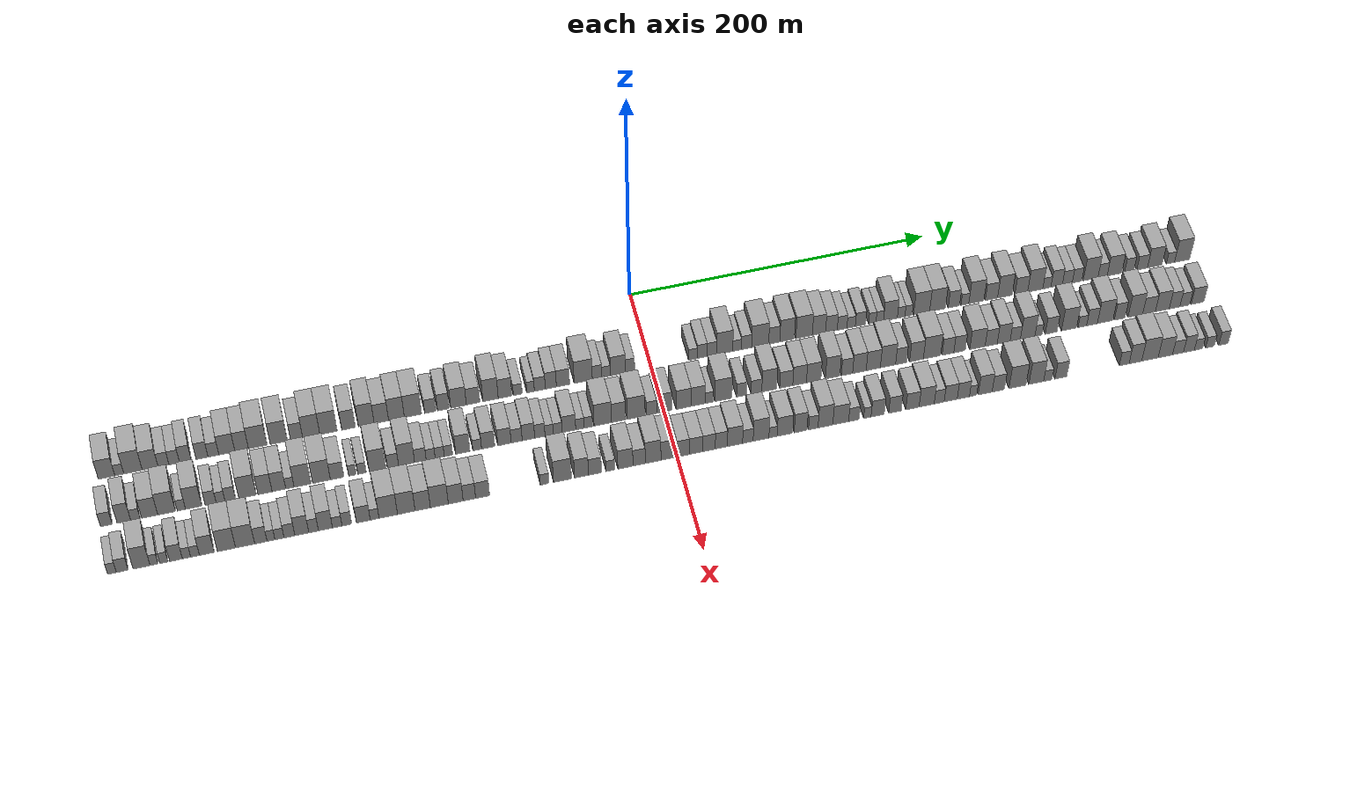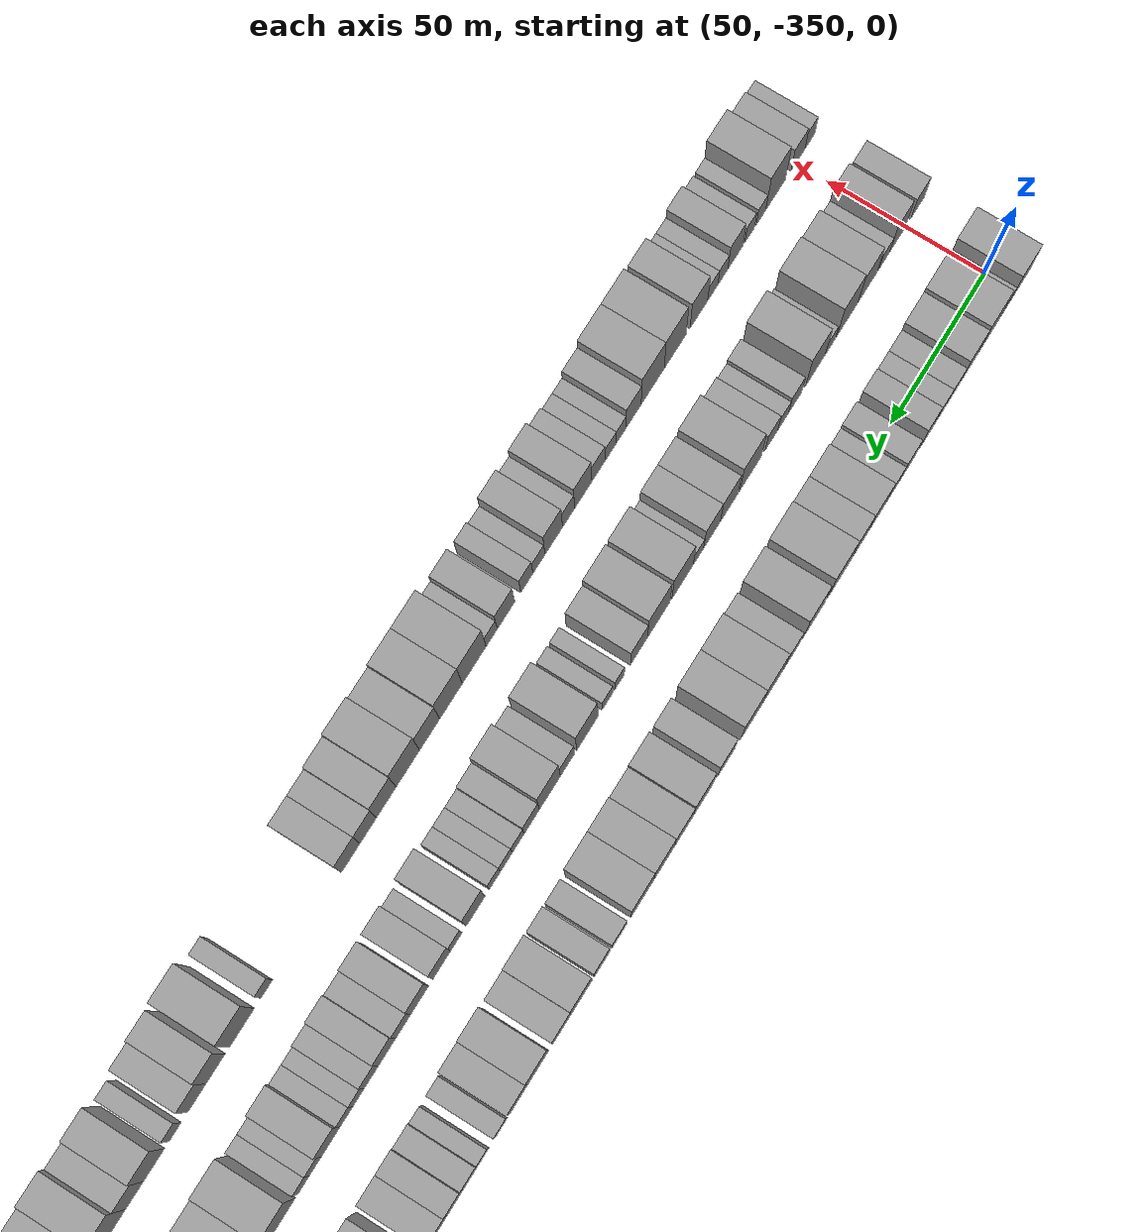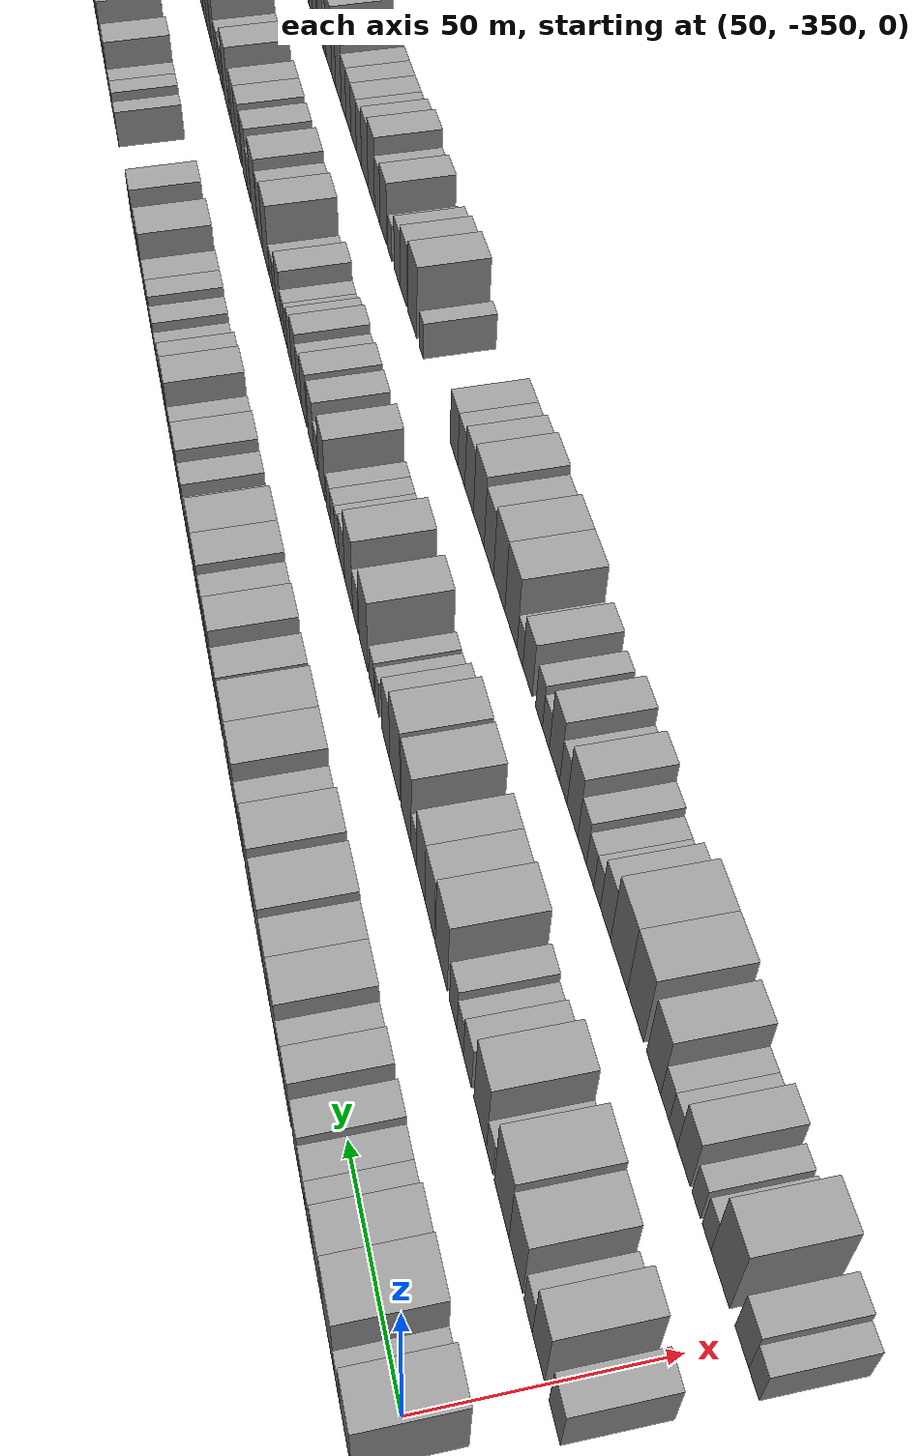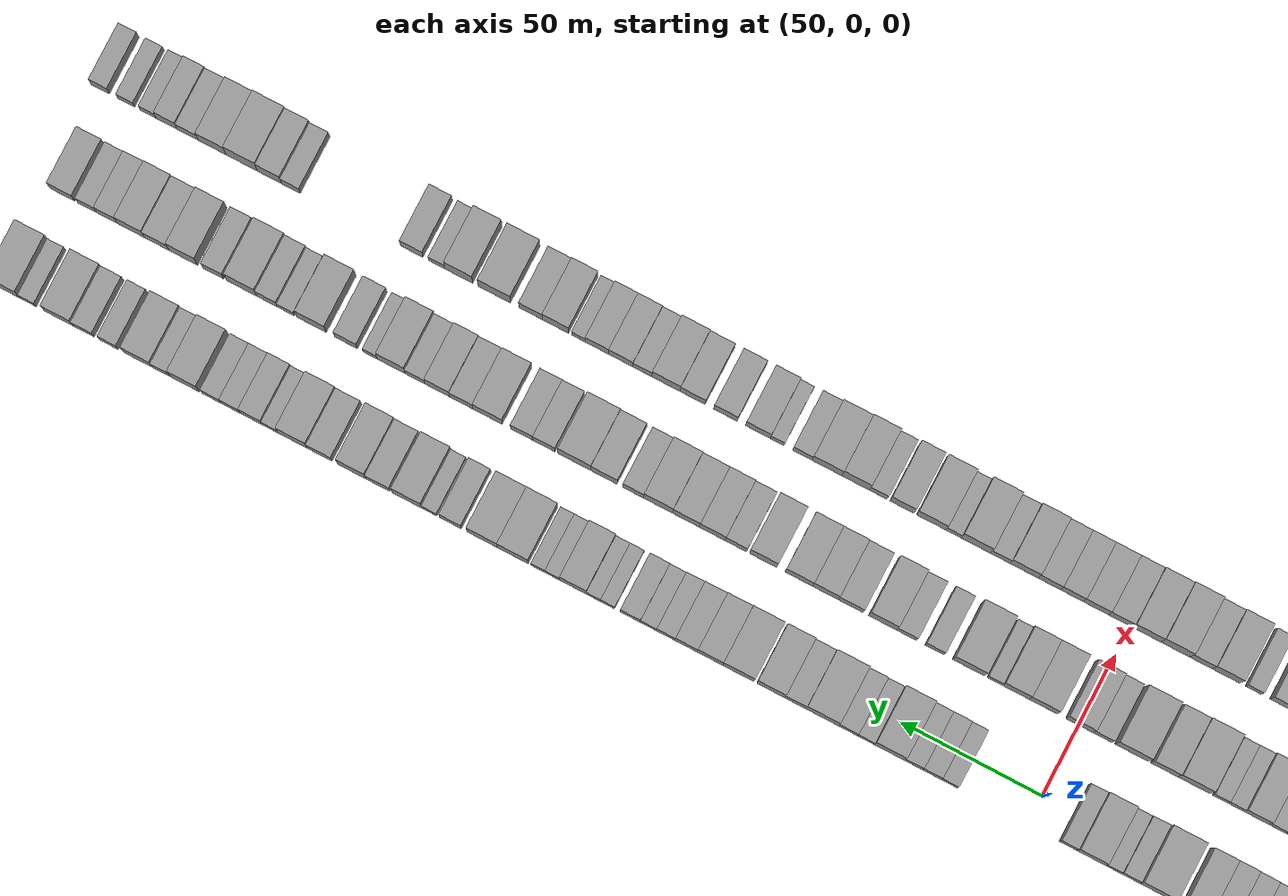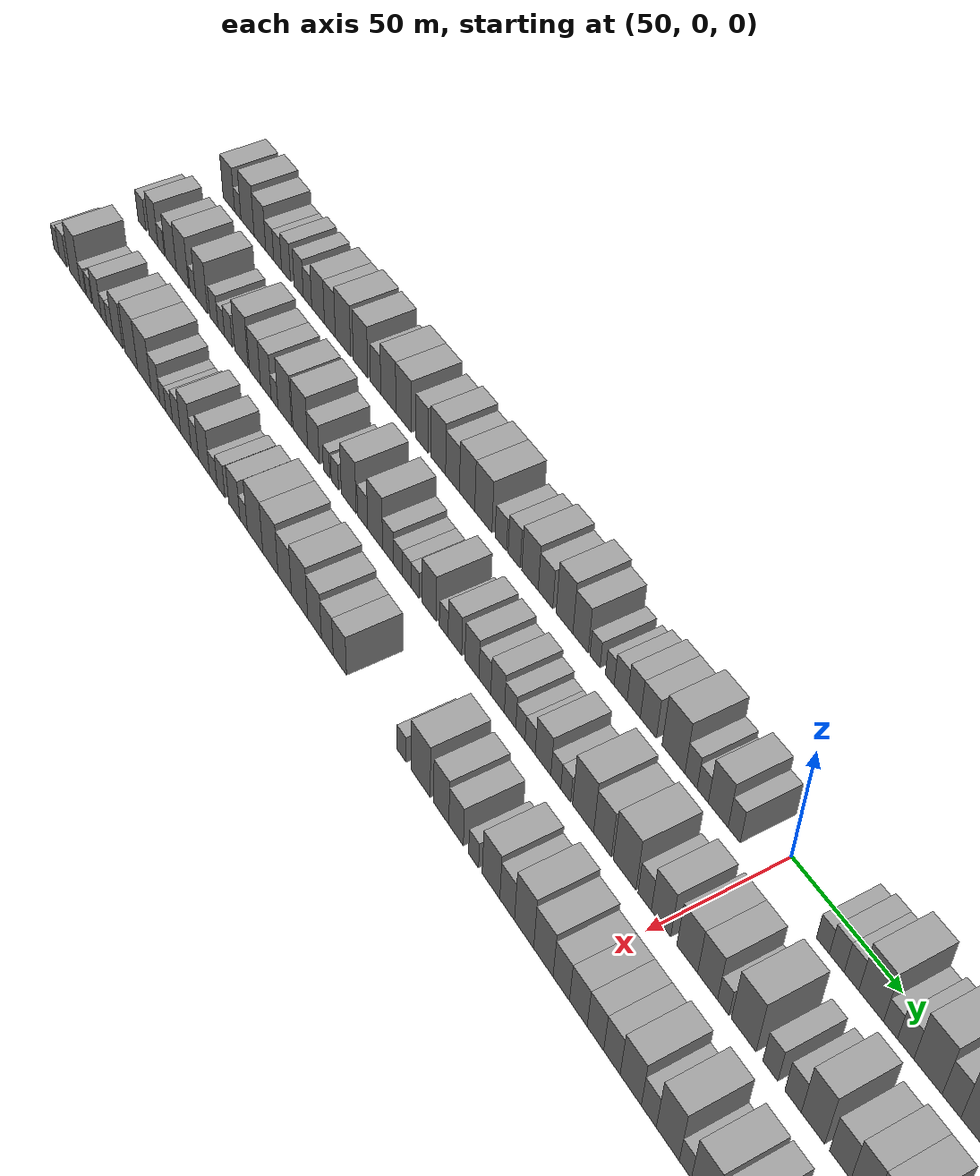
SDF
<sdf version="1.6">
 <world name="default">
  <scene>
   <sky><clouds><speed>12</speed></clouds></sky>
   <ambient>0.4 0.4 0.4 1</ambient>
   <background>0.7 0.7 0.7 1</background>
   <shadows>1</shadows>
  </scene>
  <gravity>0 0 -9.8066</gravity>
  <magnetic_field>6e-06 2.3e-05 -4.2e-05</magnetic_field>
  <physics default="0" name="default_physics" type="ode">
   <ode>
    <solver>
     <type>quick</type>
     <iters>10</iters>
     <sor>1.0</sor>
     <use_dynamic_moi_rescaling>0</use_dynamic_moi_rescaling>
    </solver>
    <constraints>
     <cfm>0</cfm>
     <erp>0.2</erp>
     <contact_max_correcting_vel>100</contact_max_correcting_vel>
     <contact_surface_layer>0.001</contact_surface_layer>
    </constraints>
   </ode>
   <max_step_size>0.004</max_step_size>
   <real_time_factor>1</real_time_factor>
   <real_time_update_rate>250</real_time_update_rate>
  </physics>
  <light name="sun" type="directional">
   <pose>0 0 10 0 0 0</pose>
   <diffuse>0.8 0.8 0.8 1</diffuse>
   <specular>0.2 0.2 0.2 1</specular>
   <attenuation>
    <range>1000</range>
    <constant>0.9</constant>
    <linear>0.01</linear>
    <quadratic>0.001</quadratic>
   </attenuation>
   <direction>-0.5 0.1 -0.9</direction>
  </light>
  <model name="building_1">
   <static>1</static>
   <pose>50.0000 -351.7952 0 0.000000 0.000000 0.000000</pose>
   <link name="link">
    <pose>0 0 10.50 0 0 0</pose>
    <collision name="collision"><geometry><box><size>20.0000 10.4095 21.0000</size></box></geometry></collision>
    <visual name="visual">
     <cast_shadows>0</cast_shadows>
     <geometry><box><size>20.0000 10.4095 21.0000</size></box></geometry>
     <material>
      <script>
       <uri>model://grey_wall/materials/scripts</uri>
       <uri>model://grey_wall/materials/textures</uri>
       <name>vrc/grey_wall</name>
      </script>
     </material>
    </visual>
   </link>
  </model>
  <model name="building_2">
   <static>1</static>
   <pose>50.0000 -343.7578 0 0.000000 0.000000 0.000000</pose>
   <link name="link">
    <pose>0 0 6.00 0 0 0</pose>
    <collision name="collision"><geometry><box><size>20.0000 5.6654 12.0000</size></box></geometry></collision>
    <visual name="visual">
     <cast_shadows>0</cast_shadows>
     <geometry><box><size>20.0000 5.6654 12.0000</size></box></geometry>
     <material>
      <script>
       <uri>model://grey_wall/materials/scripts</uri>
       <uri>model://grey_wall/materials/textures</uri>
       <name>vrc/grey_wall</name>
      </script>
     </material>
    </visual>
   </link>
  </model>
  <model name="building_3">
   <static>1</static>
   <pose>50.0000 -335.0995 0 0.000000 0.000000 0.000000</pose>
   <link name="link">
    <pose>0 0 12.00 0 0 0</pose>
    <collision name="collision"><geometry><box><size>20.0000 11.6511 24.0000</size></box></geometry></collision>
    <visual name="visual">
     <cast_shadows>0</cast_shadows>
     <geometry><box><size>20.0000 11.6511 24.0000</size></box></geometry>
     <material>
      <script>
       <uri>model://grey_wall/materials/scripts</uri>
       <uri>model://grey_wall/materials/textures</uri>
       <name>vrc/grey_wall</name>
      </script>
     </material>
    </visual>
   </link>
  </model>
  <model name="building_4">
   <static>1</static>
   <pose>50.0000 -324.2634 0 0.000000 0.000000 0.000000</pose>
   <link name="link">
    <pose>0 0 10.50 0 0 0</pose>
    <collision name="collision"><geometry><box><size>20.0000 10.0211 21.0000</size></box></geometry></collision>
    <visual name="visual">
     <cast_shadows>0</cast_shadows>
     <geometry><box><size>20.0000 10.0211 21.0000</size></box></geometry>
     <material>
      <script>
       <uri>model://grey_wall/materials/scripts</uri>
       <uri>model://grey_wall/materials/textures</uri>
       <name>vrc/grey_wall</name>
      </script>
     </material>
    </visual>
   </link>
  </model>
  <model name="building_5">
   <static>1</static>
   <pose>50.0000 -315.8424 0 0.000000 0.000000 0.000000</pose>
   <link name="link">
    <pose>0 0 7.50 0 0 0</pose>
    <collision name="collision"><geometry><box><size>20.0000 6.8208 15.0000</size></box></geometry></collision>
    <visual name="visual">
     <cast_shadows>0</cast_shadows>
     <geometry><box><size>20.0000 6.8208 15.0000</size></box></geometry>
     <material>
      <script>
       <uri>model://grey_wall/materials/scripts</uri>
       <uri>model://grey_wall/materials/textures</uri>
       <name>vrc/grey_wall</name>
      </script>
     </material>
    </visual>
   </link>
  </model>
  <model name="building_6">
   <static>1</static>
   <pose>50.0000 -309.0716 0 0.000000 0.000000 0.000000</pose>
   <link name="link">
    <pose>0 0 7.50 0 0 0</pose>
    <collision name="collision"><geometry><box><size>20.0000 6.7209 15.0000</size></box></geometry></collision>
    <visual name="visual">
     <cast_shadows>0</cast_shadows>
     <geometry><box><size>20.0000 6.7209 15.0000</size></box></geometry>
     <material>
      <script>
       <uri>model://grey_wall/materials/scripts</uri>
       <uri>model://grey_wall/materials/textures</uri>
       <name>vrc/grey_wall</name>
      </script>
     </material>
    </visual>
   </link>
  </model>
  <model name="building_7">
   <static>1</static>
   <pose>50.0000 -301.9825 0 0.000000 0.000000 0.000000</pose>
   <link name="link">
    <pose>0 0 9.00 0 0 0</pose>
    <collision name="collision"><geometry><box><size>20.0000 7.4573 18.0000</size></box></geometry></collision>
    <visual name="visual">
     <cast_shadows>0</cast_shadows>
     <geometry><box><size>20.0000 7.4573 18.0000</size></box></geometry>
     <material>
      <script>
       <uri>model://grey_wall/materials/scripts</uri>
       <uri>model://grey_wall/materials/textures</uri>
       <name>vrc/grey_wall</name>
      </script>
     </material>
    </visual>
   </link>
  </model>
  <model name="building_8">
   <static>1</static>
   <pose>50.0000 -291.4429 0 0.000000 0.000000 0.000000</pose>
   <link name="link">
    <pose>0 0 9.00 0 0 0</pose>
    <collision name="collision"><geometry><box><size>20.0000 7.6219 18.0000</size></box></geometry></collision>
    <visual name="visual">
     <cast_shadows>0</cast_shadows>
     <geometry><box><size>20.0000 7.6219 18.0000</size></box></geometry>
     <material>
      <script>
       <uri>model://grey_wall/materials/scripts</uri>
       <uri>model://grey_wall/materials/textures</uri>
       <name>vrc/grey_wall</name>
      </script>
     </material>
    </visual>
   </link>
  </model>
  <model name="building_9">
   <static>1</static>
   <pose>50.0000 -284.2054 0 0.000000 0.000000 0.000000</pose>
   <link name="link">
    <pose>0 0 7.50 0 0 0</pose>
    <collision name="collision"><geometry><box><size>20.0000 6.8531 15.0000</size></box></geometry></collision>
    <visual name="visual">
     <cast_shadows>0</cast_shadows>
     <geometry><box><size>20.0000 6.8531 15.0000</size></box></geometry>
     <material>
      <script>
       <uri>model://grey_wall/materials/scripts</uri>
       <uri>model://grey_wall/materials/textures</uri>
       <name>vrc/grey_wall</name>
      </script>
     </material>
    </visual>
   </link>
  </model>
  <model name="building_10">
   <static>1</static>
   <pose>50.0000 -275.6748 0 0.000000 0.000000 0.000000</pose>
   <link name="link">
    <pose>0 0 10.50 0 0 0</pose>
    <collision name="collision"><geometry><box><size>20.0000 10.2080 21.0000</size></box></geometry></collision>
    <visual name="visual">
     <cast_shadows>0</cast_shadows>
     <geometry><box><size>20.0000 10.2080 21.0000</size></box></geometry>
     <material>
      <script>
       <uri>model://grey_wall/materials/scripts</uri>
       <uri>model://grey_wall/materials/textures</uri>
       <name>vrc/grey_wall</name>
      </script>
     </material>
    </visual>
   </link>
  </model>
  <model name="building_11">
   <static>1</static>
   <pose>50.0000 -266.2556 0 0.000000 0.000000 0.000000</pose>
   <link name="link">
    <pose>0 0 10.50 0 0 0</pose>
    <collision name="collision"><geometry><box><size>20.0000 8.6305 21.0000</size></box></geometry></collision>
    <visual name="visual">
     <cast_shadows>0</cast_shadows>
     <geometry><box><size>20.0000 8.6305 21.0000</size></box></geometry>
     <material>
      <script>
       <uri>model://grey_wall/materials/scripts</uri>
       <uri>model://grey_wall/materials/textures</uri>
       <name>vrc/grey_wall</name>
      </script>
     </material>
    </visual>
   </link>
  </model>
  <model name="building_12">
   <static>1</static>
   <pose>50.0000 -255.9989 0 0.000000 0.000000 0.000000</pose>
   <link name="link">
    <pose>0 0 12.00 0 0 0</pose>
    <collision name="collision"><geometry><box><size>20.0000 11.8830 24.0000</size></box></geometry></collision>
    <visual name="visual">
     <cast_shadows>0</cast_shadows>
     <geometry><box><size>20.0000 11.8830 24.0000</size></box></geometry>
     <material>
      <script>
       <uri>model://grey_wall/materials/scripts</uri>
       <uri>model://grey_wall/materials/textures</uri>
       <name>vrc/grey_wall</name>
      </script>
     </material>
    </visual>
   </link>
  </model>
  <model name="building_13">
   <static>1</static>
   <pose>50.0000 -242.5805 0 0.000000 0.000000 0.000000</pose>
   <link name="link">
    <pose>0 0 12.00 0 0 0</pose>
    <collision name="collision"><geometry><box><size>20.0000 10.9537 24.0000</size></box></geometry></collision>
    <visual name="visual">
     <cast_shadows>0</cast_shadows>
     <geometry><box><size>20.0000 10.9537 24.0000</size></box></geometry>
     <material>
      <script>
       <uri>model://grey_wall/materials/scripts</uri>
       <uri>model://grey_wall/materials/textures</uri>
       <name>vrc/grey_wall</name>
      </script>
     </material>
    </visual>
   </link>
  </model>
  <model name="building_14">
   <static>1</static>
   <pose>50.0000 -231.2378 0 0.000000 0.000000 0.000000</pose>
   <link name="link">
    <pose>0 0 9.00 0 0 0</pose>
    <collision name="collision"><geometry><box><size>20.0000 7.7319 18.0000</size></box></geometry></collision>
    <visual name="visual">
     <cast_shadows>0</cast_shadows>
     <geometry><box><size>20.0000 7.7319 18.0000</size></box></geometry>
     <material>
      <script>
       <uri>model://grey_wall/materials/scripts</uri>
       <uri>model://grey_wall/materials/textures</uri>
       <name>vrc/grey_wall</name>
      </script>
     </material>
    </visual>
   </link>
  </model>
  <model name="building_15">
   <static>1</static>
   <pose>50.0000 -221.8529 0 0.000000 0.000000 0.000000</pose>
   <link name="link">
    <pose>0 0 12.00 0 0 0</pose>
    <collision name="collision"><geometry><box><size>20.0000 11.0380 24.0000</size></box></geometry></collision>
    <visual name="visual">
     <cast_shadows>0</cast_shadows>
     <geometry><box><size>20.0000 11.0380 24.0000</size></box></geometry>
     <material>
      <script>
       <uri>model://grey_wall/materials/scripts</uri>
       <uri>model://grey_wall/materials/textures</uri>
       <name>vrc/grey_wall</name>
      </script>
     </material>
    </visual>
   </link>
  </model>
  <model name="building_16">
   <static>1</static>
   <pose>50.0000 -210.7647 0 0.000000 0.000000 0.000000</pose>
   <link name="link">
    <pose>0 0 12.00 0 0 0</pose>
    <collision name="collision"><geometry><box><size>20.0000 11.1383 24.0000</size></box></geometry></collision>
    <visual name="visual">
     <cast_shadows>0</cast_shadows>
     <geometry><box><size>20.0000 11.1383 24.0000</size></box></geometry>
     <material>
      <script>
       <uri>model://grey_wall/materials/scripts</uri>
       <uri>model://grey_wall/materials/textures</uri>
       <name>vrc/grey_wall</name>
      </script>
     </material>
    </visual>
   </link>
  </model>
  <model name="building_17">
   <static>1</static>
   <pose>50.0000 -197.8496 0 0.000000 0.000000 0.000000</pose>
   <link name="link">
    <pose>0 0 10.50 0 0 0</pose>
    <collision name="collision"><geometry><box><size>20.0000 8.6920 21.0000</size></box></geometry></collision>
    <visual name="visual">
     <cast_shadows>0</cast_shadows>
     <geometry><box><size>20.0000 8.6920 21.0000</size></box></geometry>
     <material>
      <script>
       <uri>model://grey_wall/materials/scripts</uri>
       <uri>model://grey_wall/materials/textures</uri>
       <name>vrc/grey_wall</name>
      </script>
     </material>
    </visual>
   </link>
  </model>
  <model name="building_18">
   <static>1</static>
   <pose>50.0000 -186.4516 0 0.000000 0.000000 0.000000</pose>
   <link name="link">
    <pose>0 0 12.00 0 0 0</pose>
    <collision name="collision"><geometry><box><size>20.0000 10.1040 24.0000</size></box></geometry></collision>
    <visual name="visual">
     <cast_shadows>0</cast_shadows>
     <geometry><box><size>20.0000 10.1040 24.0000</size></box></geometry>
     <material>
      <script>
       <uri>model://grey_wall/materials/scripts</uri>
       <uri>model://grey_wall/materials/textures</uri>
       <name>vrc/grey_wall</name>
      </script>
     </material>
    </visual>
   </link>
  </model>
  <model name="building_19">
   <static>1</static>
   <pose>50.0000 -176.7183 0 0.000000 0.000000 0.000000</pose>
   <link name="link">
    <pose>0 0 10.50 0 0 0</pose>
    <collision name="collision"><geometry><box><size>20.0000 9.3626 21.0000</size></box></geometry></collision>
    <visual name="visual">
     <cast_shadows>0</cast_shadows>
     <geometry><box><size>20.0000 9.3626 21.0000</size></box></geometry>
     <material>
      <script>
       <uri>model://grey_wall/materials/scripts</uri>
       <uri>model://grey_wall/materials/textures</uri>
       <name>vrc/grey_wall</name>
      </script>
     </material>
    </visual>
   </link>
  </model>
  <model name="building_20">
   <static>1</static>
   <pose>50.0000 -166.9501 0 0.000000 0.000000 0.000000</pose>
   <link name="link">
    <pose>0 0 12.00 0 0 0</pose>
    <collision name="collision"><geometry><box><size>20.0000 10.1739 24.0000</size></box></geometry></collision>
    <visual name="visual">
     <cast_shadows>0</cast_shadows>
     <geometry><box><size>20.0000 10.1739 24.0000</size></box></geometry>
     <material>
      <script>
       <uri>model://grey_wall/materials/scripts</uri>
       <uri>model://grey_wall/materials/textures</uri>
       <name>vrc/grey_wall</name>
      </script>
     </material>
    </visual>
   </link>
  </model>
  <model name="building_21">
   <static>1</static>
   <pose>50.0000 -156.2615 0 0.000000 0.000000 0.000000</pose>
   <link name="link">
    <pose>0 0 12.00 0 0 0</pose>
    <collision name="collision"><geometry><box><size>20.0000 11.2033 24.0000</size></box></geometry></collision>
    <visual name="visual">
     <cast_shadows>0</cast_shadows>
     <geometry><box><size>20.0000 11.2033 24.0000</size></box></geometry>
     <material>
      <script>
       <uri>model://grey_wall/materials/scripts</uri>
       <uri>model://grey_wall/materials/textures</uri>
       <name>vrc/grey_wall</name>
      </script>
     </material>
    </visual>
   </link>
  </model>
  <model name="building_22">
   <static>1</static>
   <pose>50.0000 -144.9928 0 0.000000 0.000000 0.000000</pose>
   <link name="link">
    <pose>0 0 7.50 0 0 0</pose>
    <collision name="collision"><geometry><box><size>20.0000 7.3341 15.0000</size></box></geometry></collision>
    <visual name="visual">
     <cast_shadows>0</cast_shadows>
     <geometry><box><size>20.0000 7.3341 15.0000</size></box></geometry>
     <material>
      <script>
       <uri>model://grey_wall/materials/scripts</uri>
       <uri>model://grey_wall/materials/textures</uri>
       <name>vrc/grey_wall</name>
      </script>
     </material>
    </visual>
   </link>
  </model>
  <model name="building_23">
   <static>1</static>
   <pose>50.0000 -136.5323 0 0.000000 0.000000 0.000000</pose>
   <link name="link">
    <pose>0 0 9.00 0 0 0</pose>
    <collision name="collision"><geometry><box><size>20.0000 7.5868 18.0000</size></box></geometry></collision>
    <visual name="visual">
     <cast_shadows>0</cast_shadows>
     <geometry><box><size>20.0000 7.5868 18.0000</size></box></geometry>
     <material>
      <script>
       <uri>model://grey_wall/materials/scripts</uri>
       <uri>model://grey_wall/materials/textures</uri>
       <name>vrc/grey_wall</name>
      </script>
     </material>
    </visual>
   </link>
  </model>
  <model name="building_24">
   <static>1</static>
   <pose>50.0000 -126.6747 0 0.000000 0.000000 0.000000</pose>
   <link name="link">
    <pose>0 0 10.50 0 0 0</pose>
    <collision name="collision"><geometry><box><size>20.0000 10.1284 21.0000</size></box></geometry></collision>
    <visual name="visual">
     <cast_shadows>0</cast_shadows>
     <geometry><box><size>20.0000 10.1284 21.0000</size></box></geometry>
     <material>
      <script>
       <uri>model://grey_wall/materials/scripts</uri>
       <uri>model://grey_wall/materials/textures</uri>
       <name>vrc/grey_wall</name>
      </script>
     </material>
    </visual>
   </link>
  </model>
  <model name="building_25">
   <static>1</static>
   <pose>50.0000 -117.2045 0 0.000000 0.000000 0.000000</pose>
   <link name="link">
    <pose>0 0 9.00 0 0 0</pose>
    <collision name="collision"><geometry><box><size>20.0000 8.8121 18.0000</size></box></geometry></collision>
    <visual name="visual">
     <cast_shadows>0</cast_shadows>
     <geometry><box><size>20.0000 8.8121 18.0000</size></box></geometry>
     <material>
      <script>
       <uri>model://grey_wall/materials/scripts</uri>
       <uri>model://grey_wall/materials/textures</uri>
       <name>vrc/grey_wall</name>
      </script>
     </material>
    </visual>
   </link>
  </model>
  <model name="building_26">
   <static>1</static>
   <pose>50.0000 -105.8150 0 0.000000 0.000000 0.000000</pose>
   <link name="link">
    <pose>0 0 12.00 0 0 0</pose>
    <collision name="collision"><geometry><box><size>20.0000 9.9670 24.0000</size></box></geometry></collision>
    <visual name="visual">
     <cast_shadows>0</cast_shadows>
     <geometry><box><size>20.0000 9.9670 24.0000</size></box></geometry>
     <material>
      <script>
       <uri>model://grey_wall/materials/scripts</uri>
       <uri>model://grey_wall/materials/textures</uri>
       <name>vrc/grey_wall</name>
      </script>
     </material>
    </visual>
   </link>
  </model>
  <model name="building_27">
   <static>1</static>
   <pose>50.0000 -96.3800 0 0.000000 0.000000 0.000000</pose>
   <link name="link">
    <pose>0 0 10.50 0 0 0</pose>
    <collision name="collision"><geometry><box><size>20.0000 8.9029 21.0000</size></box></geometry></collision>
    <visual name="visual">
     <cast_shadows>0</cast_shadows>
     <geometry><box><size>20.0000 8.9029 21.0000</size></box></geometry>
     <material>
      <script>
       <uri>model://grey_wall/materials/scripts</uri>
       <uri>model://grey_wall/materials/textures</uri>
       <name>vrc/grey_wall</name>
      </script>
     </material>
    </visual>
   </link>
  </model>
  <model name="building_28">
   <static>1</static>
   <pose>50.0000 -88.0359 0 0.000000 0.000000 0.000000</pose>
   <link name="link">
    <pose>0 0 6.00 0 0 0</pose>
    <collision name="collision"><geometry><box><size>20.0000 5.7853 12.0000</size></box></geometry></collision>
    <visual name="visual">
     <cast_shadows>0</cast_shadows>
     <geometry><box><size>20.0000 5.7853 12.0000</size></box></geometry>
     <material>
      <script>
       <uri>model://grey_wall/materials/scripts</uri>
       <uri>model://grey_wall/materials/textures</uri>
       <name>vrc/grey_wall</name>
      </script>
     </material>
    </visual>
   </link>
  </model>
  <model name="building_29">
   <static>1</static>
   <pose>50.0000 -79.6568 0 0.000000 0.000000 0.000000</pose>
   <link name="link">
    <pose>0 0 6.00 0 0 0</pose>
    <collision name="collision"><geometry><box><size>20.0000 4.9729 12.0000</size></box></geometry></collision>
    <visual name="visual">
     <cast_shadows>0</cast_shadows>
     <geometry><box><size>20.0000 4.9729 12.0000</size></box></geometry>
     <material>
      <script>
       <uri>model://grey_wall/materials/scripts</uri>
       <uri>model://grey_wall/materials/textures</uri>
       <name>vrc/grey_wall</name>
      </script>
     </material>
    </visual>
   </link>
  </model>
  <model name="building_30">
   <static>1</static>
   <pose>50.0000 -73.5913 0 0.000000 0.000000 0.000000</pose>
   <link name="link">
    <pose>0 0 7.50 0 0 0</pose>
    <collision name="collision"><geometry><box><size>20.0000 7.1581 15.0000</size></box></geometry></collision>
    <visual name="visual">
     <cast_shadows>0</cast_shadows>
     <geometry><box><size>20.0000 7.1581 15.0000</size></box></geometry>
     <material>
      <script>
       <uri>model://grey_wall/materials/scripts</uri>
       <uri>model://grey_wall/materials/textures</uri>
       <name>vrc/grey_wall</name>
      </script>
     </material>
    </visual>
   </link>
  </model>
  <model name="building_31">
   <static>1</static>
   <pose>50.0000 -66.3682 0 0.000000 0.000000 0.000000</pose>
   <link name="link">
    <pose>0 0 9.00 0 0 0</pose>
    <collision name="collision"><geometry><box><size>20.0000 7.2880 18.0000</size></box></geometry></collision>
    <visual name="visual">
     <cast_shadows>0</cast_shadows>
     <geometry><box><size>20.0000 7.2880 18.0000</size></box></geometry>
     <material>
      <script>
       <uri>model://grey_wall/materials/scripts</uri>
       <uri>model://grey_wall/materials/textures</uri>
       <name>vrc/grey_wall</name>
      </script>
     </material>
    </visual>
   </link>
  </model>
  <model name="building_32">
   <static>1</static>
   <pose>50.0000 -58.3895 0 0.000000 0.000000 0.000000</pose>
   <link name="link">
    <pose>0 0 9.00 0 0 0</pose>
    <collision name="collision"><geometry><box><size>20.0000 8.6693 18.0000</size></box></geometry></collision>
    <visual name="visual">
     <cast_shadows>0</cast_shadows>
     <geometry><box><size>20.0000 8.6693 18.0000</size></box></geometry>
     <material>
      <script>
       <uri>model://grey_wall/materials/scripts</uri>
       <uri>model://grey_wall/materials/textures</uri>
       <name>vrc/grey_wall</name>
      </script>
     </material>
    </visual>
   </link>
  </model>
  <model name="building_33">
   <static>1</static>
   <pose>50.0000 -45.0629 0 0.000000 0.000000 0.000000</pose>
   <link name="link">
    <pose>0 0 12.00 0 0 0</pose>
    <collision name="collision"><geometry><box><size>20.0000 11.9839 24.0000</size></box></geometry></collision>
    <visual name="visual">
     <cast_shadows>0</cast_shadows>
     <geometry><box><size>20.0000 11.9839 24.0000</size></box></geometry>
     <material>
      <script>
       <uri>model://grey_wall/materials/scripts</uri>
       <uri>model://grey_wall/materials/textures</uri>
       <name>vrc/grey_wall</name>
      </script>
     </material>
    </visual>
   </link>
  </model>
  <model name="building_34">
   <static>1</static>
   <pose>50.0000 -35.9239 0 0.000000 0.000000 0.000000</pose>
   <link name="link">
    <pose>0 0 7.50 0 0 0</pose>
    <collision name="collision"><geometry><box><size>20.0000 6.2943 15.0000</size></box></geometry></collision>
    <visual name="visual">
     <cast_shadows>0</cast_shadows>
     <geometry><box><size>20.0000 6.2943 15.0000</size></box></geometry>
     <material>
      <script>
       <uri>model://grey_wall/materials/scripts</uri>
       <uri>model://grey_wall/materials/textures</uri>
       <name>vrc/grey_wall</name>
      </script>
     </material>
    </visual>
   </link>
  </model>
  <model name="building_35">
   <static>1</static>
   <pose>50.0000 -29.9349 0 0.000000 0.000000 0.000000</pose>
   <link name="link">
    <pose>0 0 6.00 0 0 0</pose>
    <collision name="collision"><geometry><box><size>20.0000 5.6836 12.0000</size></box></geometry></collision>
    <visual name="visual">
     <cast_shadows>0</cast_shadows>
     <geometry><box><size>20.0000 5.6836 12.0000</size></box></geometry>
     <material>
      <script>
       <uri>model://grey_wall/materials/scripts</uri>
       <uri>model://grey_wall/materials/textures</uri>
       <name>vrc/grey_wall</name>
      </script>
     </material>
    </visual>
   </link>
  </model>
  <model name="building_36">
   <static>1</static>
   <pose>50.0000 -22.1272 0 0.000000 0.000000 0.000000</pose>
   <link name="link">
    <pose>0 0 10.50 0 0 0</pose>
    <collision name="collision"><geometry><box><size>20.0000 9.9319 21.0000</size></box></geometry></collision>
    <visual name="visual">
     <cast_shadows>0</cast_shadows>
     <geometry><box><size>20.0000 9.9319 21.0000</size></box></geometry>
     <material>
      <script>
       <uri>model://grey_wall/materials/scripts</uri>
       <uri>model://grey_wall/materials/textures</uri>
       <name>vrc/grey_wall</name>
      </script>
     </material>
    </visual>
   </link>
  </model>
  <model name="building_37">
   <static>1</static>
   <pose>50.0000 -14.1544 0 0.000000 0.000000 0.000000</pose>
   <link name="link">
    <pose>0 0 7.50 0 0 0</pose>
    <collision name="collision"><geometry><box><size>20.0000 6.0138 15.0000</size></box></geometry></collision>
    <visual name="visual">
     <cast_shadows>0</cast_shadows>
     <geometry><box><size>20.0000 6.0138 15.0000</size></box></geometry>
     <material>
      <script>
       <uri>model://grey_wall/materials/scripts</uri>
       <uri>model://grey_wall/materials/textures</uri>
       <name>vrc/grey_wall</name>
      </script>
     </material>
    </visual>
   </link>
  </model>
  <model name="building_38">
   <static>1</static>
   <pose>50.0000 27.5653 0 0.000000 0.000000 0.000000</pose>
   <link name="link">
    <pose>0 0 6.00 0 0 0</pose>
    <collision name="collision"><geometry><box><size>20.0000 5.8085 12.0000</size></box></geometry></collision>
    <visual name="visual">
     <cast_shadows>0</cast_shadows>
     <geometry><box><size>20.0000 5.8085 12.0000</size></box></geometry>
     <material>
      <script>
       <uri>model://grey_wall/materials/scripts</uri>
       <uri>model://grey_wall/materials/textures</uri>
       <name>vrc/grey_wall</name>
      </script>
     </material>
    </visual>
   </link>
  </model>
  <model name="building_39">
   <static>1</static>
   <pose>50.0000 33.7548 0 0.000000 0.000000 0.000000</pose>
   <link name="link">
    <pose>0 0 7.50 0 0 0</pose>
    <collision name="collision"><geometry><box><size>20.0000 6.5705 15.0000</size></box></geometry></collision>
    <visual name="visual">
     <cast_shadows>0</cast_shadows>
     <geometry><box><size>20.0000 6.5705 15.0000</size></box></geometry>
     <material>
      <script>
       <uri>model://grey_wall/materials/scripts</uri>
       <uri>model://grey_wall/materials/textures</uri>
       <name>vrc/grey_wall</name>
      </script>
     </material>
    </visual>
   </link>
  </model>
  <model name="building_40">
   <static>1</static>
   <pose>50.0000 40.2345 0 0.000000 0.000000 0.000000</pose>
   <link name="link">
    <pose>0 0 7.50 0 0 0</pose>
    <collision name="collision"><geometry><box><size>20.0000 6.3889 15.0000</size></box></geometry></collision>
    <visual name="visual">
     <cast_shadows>0</cast_shadows>
     <geometry><box><size>20.0000 6.3889 15.0000</size></box></geometry>
     <material>
      <script>
       <uri>model://grey_wall/materials/scripts</uri>
       <uri>model://grey_wall/materials/textures</uri>
       <name>vrc/grey_wall</name>
      </script>
     </material>
    </visual>
   </link>
  </model>
  <model name="building_41">
   <static>1</static>
   <pose>50.0000 48.7555 0 0.000000 0.000000 0.000000</pose>
   <link name="link">
    <pose>0 0 12.00 0 0 0</pose>
    <collision name="collision"><geometry><box><size>20.0000 10.6532 24.0000</size></box></geometry></collision>
    <visual name="visual">
     <cast_shadows>0</cast_shadows>
     <geometry><box><size>20.0000 10.6532 24.0000</size></box></geometry>
     <material>
      <script>
       <uri>model://grey_wall/materials/scripts</uri>
       <uri>model://grey_wall/materials/textures</uri>
       <name>vrc/grey_wall</name>
      </script>
     </material>
    </visual>
   </link>
  </model>
  <model name="building_42">
   <static>1</static>
   <pose>50.0000 56.9968 0 0.000000 0.000000 0.000000</pose>
   <link name="link">
    <pose>0 0 6.00 0 0 0</pose>
    <collision name="collision"><geometry><box><size>20.0000 5.8294 12.0000</size></box></geometry></collision>
    <visual name="visual">
     <cast_shadows>0</cast_shadows>
     <geometry><box><size>20.0000 5.8294 12.0000</size></box></geometry>
     <material>
      <script>
       <uri>model://grey_wall/materials/scripts</uri>
       <uri>model://grey_wall/materials/textures</uri>
       <name>vrc/grey_wall</name>
      </script>
     </material>
    </visual>
   </link>
  </model>
  <model name="building_43">
   <static>1</static>
   <pose>50.0000 63.3026 0 0.000000 0.000000 0.000000</pose>
   <link name="link">
    <pose>0 0 7.50 0 0 0</pose>
    <collision name="collision"><geometry><box><size>20.0000 6.7822 15.0000</size></box></geometry></collision>
    <visual name="visual">
     <cast_shadows>0</cast_shadows>
     <geometry><box><size>20.0000 6.7822 15.0000</size></box></geometry>
     <material>
      <script>
       <uri>model://grey_wall/materials/scripts</uri>
       <uri>model://grey_wall/materials/textures</uri>
       <name>vrc/grey_wall</name>
      </script>
     </material>
    </visual>
   </link>
  </model>
  <model name="building_44">
   <static>1</static>
   <pose>50.0000 72.4216 0 0.000000 0.000000 0.000000</pose>
   <link name="link">
    <pose>0 0 12.00 0 0 0</pose>
    <collision name="collision"><geometry><box><size>20.0000 11.4557 24.0000</size></box></geometry></collision>
    <visual name="visual">
     <cast_shadows>0</cast_shadows>
     <geometry><box><size>20.0000 11.4557 24.0000</size></box></geometry>
     <material>
      <script>
       <uri>model://grey_wall/materials/scripts</uri>
       <uri>model://grey_wall/materials/textures</uri>
       <name>vrc/grey_wall</name>
      </script>
     </material>
    </visual>
   </link>
  </model>
  <model name="building_45">
   <static>1</static>
   <pose>50.0000 81.8781 0 0.000000 0.000000 0.000000</pose>
   <link name="link">
    <pose>0 0 9.00 0 0 0</pose>
    <collision name="collision"><geometry><box><size>20.0000 7.4574 18.0000</size></box></geometry></collision>
    <visual name="visual">
     <cast_shadows>0</cast_shadows>
     <geometry><box><size>20.0000 7.4574 18.0000</size></box></geometry>
     <material>
      <script>
       <uri>model://grey_wall/materials/scripts</uri>
       <uri>model://grey_wall/materials/textures</uri>
       <name>vrc/grey_wall</name>
      </script>
     </material>
    </visual>
   </link>
  </model>
  <model name="building_46">
   <static>1</static>
   <pose>50.0000 90.5169 0 0.000000 0.000000 0.000000</pose>
   <link name="link">
    <pose>0 0 12.00 0 0 0</pose>
    <collision name="collision"><geometry><box><size>20.0000 9.8202 24.0000</size></box></geometry></collision>
    <visual name="visual">
     <cast_shadows>0</cast_shadows>
     <geometry><box><size>20.0000 9.8202 24.0000</size></box></geometry>
     <material>
      <script>
       <uri>model://grey_wall/materials/scripts</uri>
       <uri>model://grey_wall/materials/textures</uri>
       <name>vrc/grey_wall</name>
      </script>
     </material>
    </visual>
   </link>
  </model>
  <model name="building_47">
   <static>1</static>
   <pose>50.0000 101.9559 0 0.000000 0.000000 0.000000</pose>
   <link name="link">
    <pose>0 0 12.00 0 0 0</pose>
    <collision name="collision"><geometry><box><size>20.0000 11.0579 24.0000</size></box></geometry></collision>
    <visual name="visual">
     <cast_shadows>0</cast_shadows>
     <geometry><box><size>20.0000 11.0579 24.0000</size></box></geometry>
     <material>
      <script>
       <uri>model://grey_wall/materials/scripts</uri>
       <uri>model://grey_wall/materials/textures</uri>
       <name>vrc/grey_wall</name>
      </script>
     </material>
    </visual>
   </link>
  </model>
  <model name="building_48">
   <static>1</static>
   <pose>50.0000 111.9434 0 0.000000 0.000000 0.000000</pose>
   <link name="link">
    <pose>0 0 10.50 0 0 0</pose>
    <collision name="collision"><geometry><box><size>20.0000 8.9171 21.0000</size></box></geometry></collision>
    <visual name="visual">
     <cast_shadows>0</cast_shadows>
     <geometry><box><size>20.0000 8.9171 21.0000</size></box></geometry>
     <material>
      <script>
       <uri>model://grey_wall/materials/scripts</uri>
       <uri>model://grey_wall/materials/textures</uri>
       <name>vrc/grey_wall</name>
      </script>
     </material>
    </visual>
   </link>
  </model>
  <model name="building_49">
   <static>1</static>
   <pose>50.0000 120.3547 0 0.000000 0.000000 0.000000</pose>
   <link name="link">
    <pose>0 0 9.00 0 0 0</pose>
    <collision name="collision"><geometry><box><size>20.0000 7.9056 18.0000</size></box></geometry></collision>
    <visual name="visual">
     <cast_shadows>0</cast_shadows>
     <geometry><box><size>20.0000 7.9056 18.0000</size></box></geometry>
     <material>
      <script>
       <uri>model://grey_wall/materials/scripts</uri>
       <uri>model://grey_wall/materials/textures</uri>
       <name>vrc/grey_wall</name>
      </script>
     </material>
    </visual>
   </link>
  </model>
  <model name="building_50">
   <static>1</static>
   <pose>50.0000 127.5701 0 0.000000 0.000000 0.000000</pose>
   <link name="link">
    <pose>0 0 7.50 0 0 0</pose>
    <collision name="collision"><geometry><box><size>20.0000 6.5252 15.0000</size></box></geometry></collision>
    <visual name="visual">
     <cast_shadows>0</cast_shadows>
     <geometry><box><size>20.0000 6.5252 15.0000</size></box></geometry>
     <material>
      <script>
       <uri>model://grey_wall/materials/scripts</uri>
       <uri>model://grey_wall/materials/textures</uri>
       <name>vrc/grey_wall</name>
      </script>
     </material>
    </visual>
   </link>
  </model>
  <model name="building_51">
   <static>1</static>
   <pose>50.0000 133.6937 0 0.000000 0.000000 0.000000</pose>
   <link name="link">
    <pose>0 0 6.00 0 0 0</pose>
    <collision name="collision"><geometry><box><size>20.0000 5.7220 12.0000</size></box></geometry></collision>
    <visual name="visual">
     <cast_shadows>0</cast_shadows>
     <geometry><box><size>20.0000 5.7220 12.0000</size></box></geometry>
     <material>
      <script>
       <uri>model://grey_wall/materials/scripts</uri>
       <uri>model://grey_wall/materials/textures</uri>
       <name>vrc/grey_wall</name>
      </script>
     </material>
    </visual>
   </link>
  </model>
  <model name="building_52">
   <static>1</static>
   <pose>50.0000 140.0764 0 0.000000 0.000000 0.000000</pose>
   <link name="link">
    <pose>0 0 7.50 0 0 0</pose>
    <collision name="collision"><geometry><box><size>20.0000 7.0433 15.0000</size></box></geometry></collision>
    <visual name="visual">
     <cast_shadows>0</cast_shadows>
     <geometry><box><size>20.0000 7.0433 15.0000</size></box></geometry>
     <material>
      <script>
       <uri>model://grey_wall/materials/scripts</uri>
       <uri>model://grey_wall/materials/textures</uri>
       <name>vrc/grey_wall</name>
      </script>
     </material>
    </visual>
   </link>
  </model>
  <model name="building_53">
   <static>1</static>
   <pose>50.0000 148.0953 0 0.000000 0.000000 0.000000</pose>
   <link name="link">
    <pose>0 0 6.00 0 0 0</pose>
    <collision name="collision"><geometry><box><size>20.0000 4.9945 12.0000</size></box></geometry></collision>
    <visual name="visual">
     <cast_shadows>0</cast_shadows>
     <geometry><box><size>20.0000 4.9945 12.0000</size></box></geometry>
     <material>
      <script>
       <uri>model://grey_wall/materials/scripts</uri>
       <uri>model://grey_wall/materials/textures</uri>
       <name>vrc/grey_wall</name>
      </script>
     </material>
    </visual>
   </link>
  </model>
  <model name="building_54">
   <static>1</static>
   <pose>50.0000 153.1043 0 0.000000 0.000000 0.000000</pose>
   <link name="link">
    <pose>0 0 6.00 0 0 0</pose>
    <collision name="collision"><geometry><box><size>20.0000 5.0234 12.0000</size></box></geometry></collision>
    <visual name="visual">
     <cast_shadows>0</cast_shadows>
     <geometry><box><size>20.0000 5.0234 12.0000</size></box></geometry>
     <material>
      <script>
       <uri>model://grey_wall/materials/scripts</uri>
       <uri>model://grey_wall/materials/textures</uri>
       <name>vrc/grey_wall</name>
      </script>
     </material>
    </visual>
   </link>
  </model>
  <model name="building_55">
   <static>1</static>
   <pose>50.0000 160.3275 0 0.000000 0.000000 0.000000</pose>
   <link name="link">
    <pose>0 0 10.50 0 0 0</pose>
    <collision name="collision"><geometry><box><size>20.0000 9.4230 21.0000</size></box></geometry></collision>
    <visual name="visual">
     <cast_shadows>0</cast_shadows>
     <geometry><box><size>20.0000 9.4230 21.0000</size></box></geometry>
     <material>
      <script>
       <uri>model://grey_wall/materials/scripts</uri>
       <uri>model://grey_wall/materials/textures</uri>
       <name>vrc/grey_wall</name>
      </script>
     </material>
    </visual>
   </link>
  </model>
  <model name="building_56">
   <static>1</static>
   <pose>50.0000 167.6405 0 0.000000 0.000000 0.000000</pose>
   <link name="link">
    <pose>0 0 6.00 0 0 0</pose>
    <collision name="collision"><geometry><box><size>20.0000 5.2029 12.0000</size></box></geometry></collision>
    <visual name="visual">
     <cast_shadows>0</cast_shadows>
     <geometry><box><size>20.0000 5.2029 12.0000</size></box></geometry>
     <material>
      <script>
       <uri>model://grey_wall/materials/scripts</uri>
       <uri>model://grey_wall/materials/textures</uri>
       <name>vrc/grey_wall</name>
      </script>
     </material>
    </visual>
   </link>
  </model>
  <model name="building_57">
   <static>1</static>
   <pose>50.0000 172.6614 0 0.000000 0.000000 0.000000</pose>
   <link name="link">
    <pose>0 0 6.00 0 0 0</pose>
    <collision name="collision"><geometry><box><size>20.0000 4.8389 12.0000</size></box></geometry></collision>
    <visual name="visual">
     <cast_shadows>0</cast_shadows>
     <geometry><box><size>20.0000 4.8389 12.0000</size></box></geometry>
     <material>
      <script>
       <uri>model://grey_wall/materials/scripts</uri>
       <uri>model://grey_wall/materials/textures</uri>
       <name>vrc/grey_wall</name>
      </script>
     </material>
    </visual>
   </link>
  </model>
  <model name="building_58">
   <static>1</static>
   <pose>50.0000 181.5471 0 0.000000 0.000000 0.000000</pose>
   <link name="link">
    <pose>0 0 12.00 0 0 0</pose>
    <collision name="collision"><geometry><box><size>20.0000 10.9324 24.0000</size></box></geometry></collision>
    <visual name="visual">
     <cast_shadows>0</cast_shadows>
     <geometry><box><size>20.0000 10.9324 24.0000</size></box></geometry>
     <material>
      <script>
       <uri>model://grey_wall/materials/scripts</uri>
       <uri>model://grey_wall/materials/textures</uri>
       <name>vrc/grey_wall</name>
      </script>
     </material>
    </visual>
   </link>
  </model>
  <model name="building_59">
   <static>1</static>
   <pose>50.0000 192.3717 0 0.000000 0.000000 0.000000</pose>
   <link name="link">
    <pose>0 0 12.00 0 0 0</pose>
    <collision name="collision"><geometry><box><size>20.0000 10.7169 24.0000</size></box></geometry></collision>
    <visual name="visual">
     <cast_shadows>0</cast_shadows>
     <geometry><box><size>20.0000 10.7169 24.0000</size></box></geometry>
     <material>
      <script>
       <uri>model://grey_wall/materials/scripts</uri>
       <uri>model://grey_wall/materials/textures</uri>
       <name>vrc/grey_wall</name>
      </script>
     </material>
    </visual>
   </link>
  </model>
  <model name="building_60">
   <static>1</static>
   <pose>50.0000 203.5715 0 0.000000 0.000000 0.000000</pose>
   <link name="link">
    <pose>0 0 9.00 0 0 0</pose>
    <collision name="collision"><geometry><box><size>20.0000 7.6826 18.0000</size></box></geometry></collision>
    <visual name="visual">
     <cast_shadows>0</cast_shadows>
     <geometry><box><size>20.0000 7.6826 18.0000</size></box></geometry>
     <material>
      <script>
       <uri>model://grey_wall/materials/scripts</uri>
       <uri>model://grey_wall/materials/textures</uri>
       <name>vrc/grey_wall</name>
      </script>
     </material>
    </visual>
   </link>
  </model>
  <model name="building_61">
   <static>1</static>
   <pose>50.0000 211.0909 0 0.000000 0.000000 0.000000</pose>
   <link name="link">
    <pose>0 0 6.00 0 0 0</pose>
    <collision name="collision"><geometry><box><size>20.0000 5.3562 12.0000</size></box></geometry></collision>
    <visual name="visual">
     <cast_shadows>0</cast_shadows>
     <geometry><box><size>20.0000 5.3562 12.0000</size></box></geometry>
     <material>
      <script>
       <uri>model://grey_wall/materials/scripts</uri>
       <uri>model://grey_wall/materials/textures</uri>
       <name>vrc/grey_wall</name>
      </script>
     </material>
    </visual>
   </link>
  </model>
  <model name="building_62">
   <static>1</static>
   <pose>50.0000 218.9230 0 0.000000 0.000000 0.000000</pose>
   <link name="link">
    <pose>0 0 12.00 0 0 0</pose>
    <collision name="collision"><geometry><box><size>20.0000 10.3079 24.0000</size></box></geometry></collision>
    <visual name="visual">
     <cast_shadows>0</cast_shadows>
     <geometry><box><size>20.0000 10.3079 24.0000</size></box></geometry>
     <material>
      <script>
       <uri>model://grey_wall/materials/scripts</uri>
       <uri>model://grey_wall/materials/textures</uri>
       <name>vrc/grey_wall</name>
      </script>
     </material>
    </visual>
   </link>
  </model>
  <model name="building_63">
   <static>1</static>
   <pose>50.0000 229.2952 0 0.000000 0.000000 0.000000</pose>
   <link name="link">
    <pose>0 0 9.00 0 0 0</pose>
    <collision name="collision"><geometry><box><size>20.0000 8.4365 18.0000</size></box></geometry></collision>
    <visual name="visual">
     <cast_shadows>0</cast_shadows>
     <geometry><box><size>20.0000 8.4365 18.0000</size></box></geometry>
     <material>
      <script>
       <uri>model://grey_wall/materials/scripts</uri>
       <uri>model://grey_wall/materials/textures</uri>
       <name>vrc/grey_wall</name>
      </script>
     </material>
    </visual>
   </link>
  </model>
  <model name="building_64">
   <static>1</static>
   <pose>50.0000 238.4897 0 0.000000 0.000000 0.000000</pose>
   <link name="link">
    <pose>0 0 12.00 0 0 0</pose>
    <collision name="collision"><geometry><box><size>20.0000 9.9524 24.0000</size></box></geometry></collision>
    <visual name="visual">
     <cast_shadows>0</cast_shadows>
     <geometry><box><size>20.0000 9.9524 24.0000</size></box></geometry>
     <material>
      <script>
       <uri>model://grey_wall/materials/scripts</uri>
       <uri>model://grey_wall/materials/textures</uri>
       <name>vrc/grey_wall</name>
      </script>
     </material>
    </visual>
   </link>
  </model>
  <model name="building_65">
   <static>1</static>
   <pose>50.0000 249.8258 0 0.000000 0.000000 0.000000</pose>
   <link name="link">
    <pose>0 0 9.00 0 0 0</pose>
    <collision name="collision"><geometry><box><size>20.0000 8.7198 18.0000</size></box></geometry></collision>
    <visual name="visual">
     <cast_shadows>0</cast_shadows>
     <geometry><box><size>20.0000 8.7198 18.0000</size></box></geometry>
     <material>
      <script>
       <uri>model://grey_wall/materials/scripts</uri>
       <uri>model://grey_wall/materials/textures</uri>
       <name>vrc/grey_wall</name>
      </script>
     </material>
    </visual>
   </link>
  </model>
  <model name="building_66">
   <static>1</static>
   <pose>50.0000 259.4110 0 0.000000 0.000000 0.000000</pose>
   <link name="link">
    <pose>0 0 12.00 0 0 0</pose>
    <collision name="collision"><geometry><box><size>20.0000 10.4507 24.0000</size></box></geometry></collision>
    <visual name="visual">
     <cast_shadows>0</cast_shadows>
     <geometry><box><size>20.0000 10.4507 24.0000</size></box></geometry>
     <material>
      <script>
       <uri>model://grey_wall/materials/scripts</uri>
       <uri>model://grey_wall/materials/textures</uri>
       <name>vrc/grey_wall</name>
      </script>
     </material>
    </visual>
   </link>
  </model>
  <model name="building_67">
   <static>1</static>
   <pose>50.0000 267.4481 0 0.000000 0.000000 0.000000</pose>
   <link name="link">
    <pose>0 0 6.00 0 0 0</pose>
    <collision name="collision"><geometry><box><size>20.0000 5.6235 12.0000</size></box></geometry></collision>
    <visual name="visual">
     <cast_shadows>0</cast_shadows>
     <geometry><box><size>20.0000 5.6235 12.0000</size></box></geometry>
     <material>
      <script>
       <uri>model://grey_wall/materials/scripts</uri>
       <uri>model://grey_wall/materials/textures</uri>
       <name>vrc/grey_wall</name>
      </script>
     </material>
    </visual>
   </link>
  </model>
  <model name="building_68">
   <static>1</static>
   <pose>50.0000 274.1863 0 0.000000 0.000000 0.000000</pose>
   <link name="link">
    <pose>0 0 9.00 0 0 0</pose>
    <collision name="collision"><geometry><box><size>20.0000 7.8528 18.0000</size></box></geometry></collision>
    <visual name="visual">
     <cast_shadows>0</cast_shadows>
     <geometry><box><size>20.0000 7.8528 18.0000</size></box></geometry>
     <material>
      <script>
       <uri>model://grey_wall/materials/scripts</uri>
       <uri>model://grey_wall/materials/textures</uri>
       <name>vrc/grey_wall</name>
      </script>
     </material>
    </visual>
   </link>
  </model>
  <model name="building_69">
   <static>1</static>
   <pose>50.0000 281.5265 0 0.000000 0.000000 0.000000</pose>
   <link name="link">
    <pose>0 0 7.50 0 0 0</pose>
    <collision name="collision"><geometry><box><size>20.0000 6.8278 15.0000</size></box></geometry></collision>
    <visual name="visual">
     <cast_shadows>0</cast_shadows>
     <geometry><box><size>20.0000 6.8278 15.0000</size></box></geometry>
     <material>
      <script>
       <uri>model://grey_wall/materials/scripts</uri>
       <uri>model://grey_wall/materials/textures</uri>
       <name>vrc/grey_wall</name>
      </script>
     </material>
    </visual>
   </link>
  </model>
  <model name="building_70">
   <static>1</static>
   <pose>50.0000 288.2438 0 0.000000 0.000000 0.000000</pose>
   <link name="link">
    <pose>0 0 7.50 0 0 0</pose>
    <collision name="collision"><geometry><box><size>20.0000 6.6067 15.0000</size></box></geometry></collision>
    <visual name="visual">
     <cast_shadows>0</cast_shadows>
     <geometry><box><size>20.0000 6.6067 15.0000</size></box></geometry>
     <material>
      <script>
       <uri>model://grey_wall/materials/scripts</uri>
       <uri>model://grey_wall/materials/textures</uri>
       <name>vrc/grey_wall</name>
      </script>
     </material>
    </visual>
   </link>
  </model>
  <model name="building_71">
   <static>1</static>
   <pose>50.0000 297.6595 0 0.000000 0.000000 0.000000</pose>
   <link name="link">
    <pose>0 0 12.00 0 0 0</pose>
    <collision name="collision"><geometry><box><size>20.0000 10.2246 24.0000</size></box></geometry></collision>
    <visual name="visual">
     <cast_shadows>0</cast_shadows>
     <geometry><box><size>20.0000 10.2246 24.0000</size></box></geometry>
     <material>
      <script>
       <uri>model://grey_wall/materials/scripts</uri>
       <uri>model://grey_wall/materials/textures</uri>
       <name>vrc/grey_wall</name>
      </script>
     </material>
    </visual>
   </link>
  </model>
  <model name="building_72">
   <static>1</static>
   <pose>50.0000 305.9735 0 0.000000 0.000000 0.000000</pose>
   <link name="link">
    <pose>0 0 7.50 0 0 0</pose>
    <collision name="collision"><geometry><box><size>20.0000 6.4033 15.0000</size></box></geometry></collision>
    <visual name="visual">
     <cast_shadows>0</cast_shadows>
     <geometry><box><size>20.0000 6.4033 15.0000</size></box></geometry>
     <material>
      <script>
       <uri>model://grey_wall/materials/scripts</uri>
       <uri>model://grey_wall/materials/textures</uri>
       <name>vrc/grey_wall</name>
      </script>
     </material>
    </visual>
   </link>
  </model>
  <model name="building_73">
   <static>1</static>
   <pose>50.0000 314.2457 0 0.000000 0.000000 0.000000</pose>
   <link name="link">
    <pose>0 0 10.50 0 0 0</pose>
    <collision name="collision"><geometry><box><size>20.0000 10.1412 21.0000</size></box></geometry></collision>
    <visual name="visual">
     <cast_shadows>0</cast_shadows>
     <geometry><box><size>20.0000 10.1412 21.0000</size></box></geometry>
     <material>
      <script>
       <uri>model://grey_wall/materials/scripts</uri>
       <uri>model://grey_wall/materials/textures</uri>
       <name>vrc/grey_wall</name>
      </script>
     </material>
    </visual>
   </link>
  </model>
  <model name="building_74">
   <static>1</static>
   <pose>50.0000 324.5699 0 0.000000 0.000000 0.000000</pose>
   <link name="link">
    <pose>0 0 7.50 0 0 0</pose>
    <collision name="collision"><geometry><box><size>20.0000 6.5073 15.0000</size></box></geometry></collision>
    <visual name="visual">
     <cast_shadows>0</cast_shadows>
     <geometry><box><size>20.0000 6.5073 15.0000</size></box></geometry>
     <material>
      <script>
       <uri>model://grey_wall/materials/scripts</uri>
       <uri>model://grey_wall/materials/textures</uri>
       <name>vrc/grey_wall</name>
      </script>
     </material>
    </visual>
   </link>
  </model>
  <model name="building_75">
   <static>1</static>
   <pose>50.0000 333.5263 0 0.000000 0.000000 0.000000</pose>
   <link name="link">
    <pose>0 0 7.50 0 0 0</pose>
    <collision name="collision"><geometry><box><size>20.0000 7.4054 15.0000</size></box></geometry></collision>
    <visual name="visual">
     <cast_shadows>0</cast_shadows>
     <geometry><box><size>20.0000 7.4054 15.0000</size></box></geometry>
     <material>
      <script>
       <uri>model://grey_wall/materials/scripts</uri>
       <uri>model://grey_wall/materials/textures</uri>
       <name>vrc/grey_wall</name>
      </script>
     </material>
    </visual>
   </link>
  </model>
  <model name="building_76">
   <static>1</static>
   <pose>50.0000 342.3427 0 0.000000 0.000000 0.000000</pose>
   <link name="link">
    <pose>0 0 10.50 0 0 0</pose>
    <collision name="collision"><geometry><box><size>20.0000 10.2273 21.0000</size></box></geometry></collision>
    <visual name="visual">
     <cast_shadows>0</cast_shadows>
     <geometry><box><size>20.0000 10.2273 21.0000</size></box></geometry>
     <material>
      <script>
       <uri>model://grey_wall/materials/scripts</uri>
       <uri>model://grey_wall/materials/textures</uri>
       <name>vrc/grey_wall</name>
      </script>
     </material>
    </visual>
   </link>
  </model>
  <model name="building_77">
   <static>1</static>
   <pose>50.0000 353.3119 0 0.000000 0.000000 0.000000</pose>
   <link name="link">
    <pose>0 0 6.00 0 0 0</pose>
    <collision name="collision"><geometry><box><size>20.0000 5.7110 12.0000</size></box></geometry></collision>
    <visual name="visual">
     <cast_shadows>0</cast_shadows>
     <geometry><box><size>20.0000 5.7110 12.0000</size></box></geometry>
     <material>
      <script>
       <uri>model://grey_wall/materials/scripts</uri>
       <uri>model://grey_wall/materials/textures</uri>
       <name>vrc/grey_wall</name>
      </script>
     </material>
    </visual>
   </link>
  </model>
  <model name="building_78">
   <static>1</static>
   <pose>50.0000 361.4335 0 0.000000 0.000000 0.000000</pose>
   <link name="link">
    <pose>0 0 12.00 0 0 0</pose>
    <collision name="collision"><geometry><box><size>20.0000 10.5321 24.0000</size></box></geometry></collision>
    <visual name="visual">
     <cast_shadows>0</cast_shadows>
     <geometry><box><size>20.0000 10.5321 24.0000</size></box></geometry>
     <material>
      <script>
       <uri>model://grey_wall/materials/scripts</uri>
       <uri>model://grey_wall/materials/textures</uri>
       <name>vrc/grey_wall</name>
      </script>
     </material>
    </visual>
   </link>
  </model>
  <model name="building_79">
   <static>1</static>
   <pose>85.0000 -356.3077 0 0.000000 0.000000 0.000000</pose>
   <link name="link">
    <pose>0 0 7.50 0 0 0</pose>
    <collision name="collision"><geometry><box><size>20.0000 7.3847 15.0000</size></box></geometry></collision>
    <visual name="visual">
     <cast_shadows>0</cast_shadows>
     <geometry><box><size>20.0000 7.3847 15.0000</size></box></geometry>
     <material>
      <script>
       <uri>model://grey_wall/materials/scripts</uri>
       <uri>model://grey_wall/materials/textures</uri>
       <name>vrc/grey_wall</name>
      </script>
     </material>
    </visual>
   </link>
  </model>
  <model name="building_80">
   <static>1</static>
   <pose>85.0000 -345.3940 0 0.000000 0.000000 0.000000</pose>
   <link name="link">
    <pose>0 0 10.50 0 0 0</pose>
    <collision name="collision"><geometry><box><size>20.0000 8.4427 21.0000</size></box></geometry></collision>
    <visual name="visual">
     <cast_shadows>0</cast_shadows>
     <geometry><box><size>20.0000 8.4427 21.0000</size></box></geometry>
     <material>
      <script>
       <uri>model://grey_wall/materials/scripts</uri>
       <uri>model://grey_wall/materials/textures</uri>
       <name>vrc/grey_wall</name>
      </script>
     </material>
    </visual>
   </link>
  </model>
  <model name="building_81">
   <static>1</static>
   <pose>85.0000 -338.2270 0 0.000000 0.000000 0.000000</pose>
   <link name="link">
    <pose>0 0 6.00 0 0 0</pose>
    <collision name="collision"><geometry><box><size>20.0000 5.8913 12.0000</size></box></geometry></collision>
    <visual name="visual">
     <cast_shadows>0</cast_shadows>
     <geometry><box><size>20.0000 5.8913 12.0000</size></box></geometry>
     <material>
      <script>
       <uri>model://grey_wall/materials/scripts</uri>
       <uri>model://grey_wall/materials/textures</uri>
       <name>vrc/grey_wall</name>
      </script>
     </material>
    </visual>
   </link>
  </model>
  <model name="building_82">
   <static>1</static>
   <pose>85.0000 -329.2513 0 0.000000 0.000000 0.000000</pose>
   <link name="link">
    <pose>0 0 10.50 0 0 0</pose>
    <collision name="collision"><geometry><box><size>20.0000 10.0602 21.0000</size></box></geometry></collision>
    <visual name="visual">
     <cast_shadows>0</cast_shadows>
     <geometry><box><size>20.0000 10.0602 21.0000</size></box></geometry>
     <material>
      <script>
       <uri>model://grey_wall/materials/scripts</uri>
       <uri>model://grey_wall/materials/textures</uri>
       <name>vrc/grey_wall</name>
      </script>
     </material>
    </visual>
   </link>
  </model>
  <model name="building_83">
   <static>1</static>
   <pose>85.0000 -318.6643 0 0.000000 0.000000 0.000000</pose>
   <link name="link">
    <pose>0 0 12.00 0 0 0</pose>
    <collision name="collision"><geometry><box><size>20.0000 11.1138 24.0000</size></box></geometry></collision>
    <visual name="visual">
     <cast_shadows>0</cast_shadows>
     <geometry><box><size>20.0000 11.1138 24.0000</size></box></geometry>
     <material>
      <script>
       <uri>model://grey_wall/materials/scripts</uri>
       <uri>model://grey_wall/materials/textures</uri>
       <name>vrc/grey_wall</name>
      </script>
     </material>
    </visual>
   </link>
  </model>
  <model name="building_84">
   <static>1</static>
   <pose>85.0000 -309.5032 0 0.000000 0.000000 0.000000</pose>
   <link name="link">
    <pose>0 0 6.00 0 0 0</pose>
    <collision name="collision"><geometry><box><size>20.0000 5.2084 12.0000</size></box></geometry></collision>
    <visual name="visual">
     <cast_shadows>0</cast_shadows>
     <geometry><box><size>20.0000 5.2084 12.0000</size></box></geometry>
     <material>
      <script>
       <uri>model://grey_wall/materials/scripts</uri>
       <uri>model://grey_wall/materials/textures</uri>
       <name>vrc/grey_wall</name>
      </script>
     </material>
    </visual>
   </link>
  </model>
  <model name="building_85">
   <static>1</static>
   <pose>85.0000 -301.7518 0 0.000000 0.000000 0.000000</pose>
   <link name="link">
    <pose>0 0 12.00 0 0 0</pose>
    <collision name="collision"><geometry><box><size>20.0000 10.2945 24.0000</size></box></geometry></collision>
    <visual name="visual">
     <cast_shadows>0</cast_shadows>
     <geometry><box><size>20.0000 10.2945 24.0000</size></box></geometry>
     <material>
      <script>
       <uri>model://grey_wall/materials/scripts</uri>
       <uri>model://grey_wall/materials/textures</uri>
       <name>vrc/grey_wall</name>
      </script>
     </material>
    </visual>
   </link>
  </model>
  <model name="building_86">
   <static>1</static>
   <pose>85.0000 -291.1583 0 0.000000 0.000000 0.000000</pose>
   <link name="link">
    <pose>0 0 7.50 0 0 0</pose>
    <collision name="collision"><geometry><box><size>20.0000 6.8925 15.0000</size></box></geometry></collision>
    <visual name="visual">
     <cast_shadows>0</cast_shadows>
     <geometry><box><size>20.0000 6.8925 15.0000</size></box></geometry>
     <material>
      <script>
       <uri>model://grey_wall/materials/scripts</uri>
       <uri>model://grey_wall/materials/textures</uri>
       <name>vrc/grey_wall</name>
      </script>
     </material>
    </visual>
   </link>
  </model>
  <model name="building_87">
   <static>1</static>
   <pose>85.0000 -284.9317 0 0.000000 0.000000 0.000000</pose>
   <link name="link">
    <pose>0 0 6.00 0 0 0</pose>
    <collision name="collision"><geometry><box><size>20.0000 5.5606 12.0000</size></box></geometry></collision>
    <visual name="visual">
     <cast_shadows>0</cast_shadows>
     <geometry><box><size>20.0000 5.5606 12.0000</size></box></geometry>
     <material>
      <script>
       <uri>model://grey_wall/materials/scripts</uri>
       <uri>model://grey_wall/materials/textures</uri>
       <name>vrc/grey_wall</name>
      </script>
     </material>
    </visual>
   </link>
  </model>
  <model name="building_88">
   <static>1</static>
   <pose>85.0000 -278.8110 0 0.000000 0.000000 0.000000</pose>
   <link name="link">
    <pose>0 0 7.50 0 0 0</pose>
    <collision name="collision"><geometry><box><size>20.0000 6.6809 15.0000</size></box></geometry></collision>
    <visual name="visual">
     <cast_shadows>0</cast_shadows>
     <geometry><box><size>20.0000 6.6809 15.0000</size></box></geometry>
     <material>
      <script>
       <uri>model://grey_wall/materials/scripts</uri>
       <uri>model://grey_wall/materials/textures</uri>
       <name>vrc/grey_wall</name>
      </script>
     </material>
    </visual>
   </link>
  </model>
  <model name="building_89">
   <static>1</static>
   <pose>85.0000 -267.9307 0 0.000000 0.000000 0.000000</pose>
   <link name="link">
    <pose>0 0 12.00 0 0 0</pose>
    <collision name="collision"><geometry><box><size>20.0000 11.0797 24.0000</size></box></geometry></collision>
    <visual name="visual">
     <cast_shadows>0</cast_shadows>
     <geometry><box><size>20.0000 11.0797 24.0000</size></box></geometry>
     <material>
      <script>
       <uri>model://grey_wall/materials/scripts</uri>
       <uri>model://grey_wall/materials/textures</uri>
       <name>vrc/grey_wall</name>
      </script>
     </material>
    </visual>
   </link>
  </model>
  <model name="building_90">
   <static>1</static>
   <pose>85.0000 -256.9247 0 0.000000 0.000000 0.000000</pose>
   <link name="link">
    <pose>0 0 10.50 0 0 0</pose>
    <collision name="collision"><geometry><box><size>20.0000 8.9323 21.0000</size></box></geometry></collision>
    <visual name="visual">
     <cast_shadows>0</cast_shadows>
     <geometry><box><size>20.0000 8.9323 21.0000</size></box></geometry>
     <material>
      <script>
       <uri>model://grey_wall/materials/scripts</uri>
       <uri>model://grey_wall/materials/textures</uri>
       <name>vrc/grey_wall</name>
      </script>
     </material>
    </visual>
   </link>
  </model>
  <model name="building_91">
   <static>1</static>
   <pose>85.0000 -248.1477 0 0.000000 0.000000 0.000000</pose>
   <link name="link">
    <pose>0 0 10.50 0 0 0</pose>
    <collision name="collision"><geometry><box><size>20.0000 8.6215 21.0000</size></box></geometry></collision>
    <visual name="visual">
     <cast_shadows>0</cast_shadows>
     <geometry><box><size>20.0000 8.6215 21.0000</size></box></geometry>
     <material>
      <script>
       <uri>model://grey_wall/materials/scripts</uri>
       <uri>model://grey_wall/materials/textures</uri>
       <name>vrc/grey_wall</name>
      </script>
     </material>
    </visual>
   </link>
  </model>
  <model name="building_92">
   <static>1</static>
   <pose>85.0000 -241.2000 0 0.000000 0.000000 0.000000</pose>
   <link name="link">
    <pose>0 0 6.00 0 0 0</pose>
    <collision name="collision"><geometry><box><size>20.0000 5.2738 12.0000</size></box></geometry></collision>
    <visual name="visual">
     <cast_shadows>0</cast_shadows>
     <geometry><box><size>20.0000 5.2738 12.0000</size></box></geometry>
     <material>
      <script>
       <uri>model://grey_wall/materials/scripts</uri>
       <uri>model://grey_wall/materials/textures</uri>
       <name>vrc/grey_wall</name>
      </script>
     </material>
    </visual>
   </link>
  </model>
  <model name="building_93">
   <static>1</static>
   <pose>85.0000 -233.1885 0 0.000000 0.000000 0.000000</pose>
   <link name="link">
    <pose>0 0 12.00 0 0 0</pose>
    <collision name="collision"><geometry><box><size>20.0000 10.7492 24.0000</size></box></geometry></collision>
    <visual name="visual">
     <cast_shadows>0</cast_shadows>
     <geometry><box><size>20.0000 10.7492 24.0000</size></box></geometry>
     <material>
      <script>
       <uri>model://grey_wall/materials/scripts</uri>
       <uri>model://grey_wall/materials/textures</uri>
       <name>vrc/grey_wall</name>
      </script>
     </material>
    </visual>
   </link>
  </model>
  <model name="building_94">
   <static>1</static>
   <pose>85.0000 -221.1884 0 0.000000 0.000000 0.000000</pose>
   <link name="link">
    <pose>0 0 12.00 0 0 0</pose>
    <collision name="collision"><geometry><box><size>20.0000 11.2509 24.0000</size></box></geometry></collision>
    <visual name="visual">
     <cast_shadows>0</cast_shadows>
     <geometry><box><size>20.0000 11.2509 24.0000</size></box></geometry>
     <material>
      <script>
       <uri>model://grey_wall/materials/scripts</uri>
       <uri>model://grey_wall/materials/textures</uri>
       <name>vrc/grey_wall</name>
      </script>
     </material>
    </visual>
   </link>
  </model>
  <model name="building_95">
   <static>1</static>
   <pose>85.0000 -211.2373 0 0.000000 0.000000 0.000000</pose>
   <link name="link">
    <pose>0 0 9.00 0 0 0</pose>
    <collision name="collision"><geometry><box><size>20.0000 8.6513 18.0000</size></box></geometry></collision>
    <visual name="visual">
     <cast_shadows>0</cast_shadows>
     <geometry><box><size>20.0000 8.6513 18.0000</size></box></geometry>
     <material>
      <script>
       <uri>model://grey_wall/materials/scripts</uri>
       <uri>model://grey_wall/materials/textures</uri>
       <name>vrc/grey_wall</name>
      </script>
     </material>
    </visual>
   </link>
  </model>
  <model name="building_96">
   <static>1</static>
   <pose>85.0000 -201.5015 0 0.000000 0.000000 0.000000</pose>
   <link name="link">
    <pose>0 0 6.00 0 0 0</pose>
    <collision name="collision"><geometry><box><size>20.0000 4.8203 12.0000</size></box></geometry></collision>
    <visual name="visual">
     <cast_shadows>0</cast_shadows>
     <geometry><box><size>20.0000 4.8203 12.0000</size></box></geometry>
     <material>
      <script>
       <uri>model://grey_wall/materials/scripts</uri>
       <uri>model://grey_wall/materials/textures</uri>
       <name>vrc/grey_wall</name>
      </script>
     </material>
    </visual>
   </link>
  </model>
  <model name="building_97">
   <static>1</static>
   <pose>85.0000 -195.4297 0 0.000000 0.000000 0.000000</pose>
   <link name="link">
    <pose>0 0 6.00 0 0 0</pose>
    <collision name="collision"><geometry><box><size>20.0000 5.3233 12.0000</size></box></geometry></collision>
    <visual name="visual">
     <cast_shadows>0</cast_shadows>
     <geometry><box><size>20.0000 5.3233 12.0000</size></box></geometry>
     <material>
      <script>
       <uri>model://grey_wall/materials/scripts</uri>
       <uri>model://grey_wall/materials/textures</uri>
       <name>vrc/grey_wall</name>
      </script>
     </material>
    </visual>
   </link>
  </model>
  <model name="building_98">
   <static>1</static>
   <pose>85.0000 -185.4646 0 0.000000 0.000000 0.000000</pose>
   <link name="link">
    <pose>0 0 12.00 0 0 0</pose>
    <collision name="collision"><geometry><box><size>20.0000 10.6071 24.0000</size></box></geometry></collision>
    <visual name="visual">
     <cast_shadows>0</cast_shadows>
     <geometry><box><size>20.0000 10.6071 24.0000</size></box></geometry>
     <material>
      <script>
       <uri>model://grey_wall/materials/scripts</uri>
       <uri>model://grey_wall/materials/textures</uri>
       <name>vrc/grey_wall</name>
      </script>
     </material>
    </visual>
   </link>
  </model>
  <model name="building_99">
   <static>1</static>
   <pose>85.0000 -175.6319 0 0.000000 0.000000 0.000000</pose>
   <link name="link">
    <pose>0 0 7.50 0 0 0</pose>
    <collision name="collision"><geometry><box><size>20.0000 7.0582 15.0000</size></box></geometry></collision>
    <visual name="visual">
     <cast_shadows>0</cast_shadows>
     <geometry><box><size>20.0000 7.0582 15.0000</size></box></geometry>
     <material>
      <script>
       <uri>model://grey_wall/materials/scripts</uri>
       <uri>model://grey_wall/materials/textures</uri>
       <name>vrc/grey_wall</name>
      </script>
     </material>
    </visual>
   </link>
  </model>
  <model name="building_100">
   <static>1</static>
   <pose>85.0000 -166.9667 0 0.000000 0.000000 0.000000</pose>
   <link name="link">
    <pose>0 0 12.00 0 0 0</pose>
    <collision name="collision"><geometry><box><size>20.0000 10.2723 24.0000</size></box></geometry></collision>
    <visual name="visual">
     <cast_shadows>0</cast_shadows>
     <geometry><box><size>20.0000 10.2723 24.0000</size></box></geometry>
     <material>
      <script>
       <uri>model://grey_wall/materials/scripts</uri>
       <uri>model://grey_wall/materials/textures</uri>
       <name>vrc/grey_wall</name>
      </script>
     </material>
    </visual>
   </link>
  </model>
  <model name="building_101">
   <static>1</static>
   <pose>85.0000 -158.1169 0 0.000000 0.000000 0.000000</pose>
   <link name="link">
    <pose>0 0 7.50 0 0 0</pose>
    <collision name="collision"><geometry><box><size>20.0000 7.4273 15.0000</size></box></geometry></collision>
    <visual name="visual">
     <cast_shadows>0</cast_shadows>
     <geometry><box><size>20.0000 7.4273 15.0000</size></box></geometry>
     <material>
      <script>
       <uri>model://grey_wall/materials/scripts</uri>
       <uri>model://grey_wall/materials/textures</uri>
       <name>vrc/grey_wall</name>
      </script>
     </material>
    </visual>
   </link>
  </model>
  <model name="building_102">
   <static>1</static>
   <pose>85.0000 -151.5173 0 0.000000 0.000000 0.000000</pose>
   <link name="link">
    <pose>0 0 6.00 0 0 0</pose>
    <collision name="collision"><geometry><box><size>20.0000 5.7720 12.0000</size></box></geometry></collision>
    <visual name="visual">
     <cast_shadows>0</cast_shadows>
     <geometry><box><size>20.0000 5.7720 12.0000</size></box></geometry>
     <material>
      <script>
       <uri>model://grey_wall/materials/scripts</uri>
       <uri>model://grey_wall/materials/textures</uri>
       <name>vrc/grey_wall</name>
      </script>
     </material>
    </visual>
   </link>
  </model>
  <model name="building_103">
   <static>1</static>
   <pose>85.0000 -145.7244 0 0.000000 0.000000 0.000000</pose>
   <link name="link">
    <pose>0 0 6.00 0 0 0</pose>
    <collision name="collision"><geometry><box><size>20.0000 5.8138 12.0000</size></box></geometry></collision>
    <visual name="visual">
     <cast_shadows>0</cast_shadows>
     <geometry><box><size>20.0000 5.8138 12.0000</size></box></geometry>
     <material>
      <script>
       <uri>model://grey_wall/materials/scripts</uri>
       <uri>model://grey_wall/materials/textures</uri>
       <name>vrc/grey_wall</name>
      </script>
     </material>
    </visual>
   </link>
  </model>
  <model name="building_104">
   <static>1</static>
   <pose>85.0000 -140.1190 0 0.000000 0.000000 0.000000</pose>
   <link name="link">
    <pose>0 0 6.00 0 0 0</pose>
    <collision name="collision"><geometry><box><size>20.0000 5.3971 12.0000</size></box></geometry></collision>
    <visual name="visual">
     <cast_shadows>0</cast_shadows>
     <geometry><box><size>20.0000 5.3971 12.0000</size></box></geometry>
     <material>
      <script>
       <uri>model://grey_wall/materials/scripts</uri>
       <uri>model://grey_wall/materials/textures</uri>
       <name>vrc/grey_wall</name>
      </script>
     </material>
    </visual>
   </link>
  </model>
  <model name="building_105">
   <static>1</static>
   <pose>85.0000 -130.8782 0 0.000000 0.000000 0.000000</pose>
   <link name="link">
    <pose>0 0 10.50 0 0 0</pose>
    <collision name="collision"><geometry><box><size>20.0000 9.0844 21.0000</size></box></geometry></collision>
    <visual name="visual">
     <cast_shadows>0</cast_shadows>
     <geometry><box><size>20.0000 9.0844 21.0000</size></box></geometry>
     <material>
      <script>
       <uri>model://grey_wall/materials/scripts</uri>
       <uri>model://grey_wall/materials/textures</uri>
       <name>vrc/grey_wall</name>
      </script>
     </material>
    </visual>
   </link>
  </model>
  <model name="building_106">
   <static>1</static>
   <pose>85.0000 -121.5744 0 0.000000 0.000000 0.000000</pose>
   <link name="link">
    <pose>0 0 6.00 0 0 0</pose>
    <collision name="collision"><geometry><box><size>20.0000 5.5231 12.0000</size></box></geometry></collision>
    <visual name="visual">
     <cast_shadows>0</cast_shadows>
     <geometry><box><size>20.0000 5.5231 12.0000</size></box></geometry>
     <material>
      <script>
       <uri>model://grey_wall/materials/scripts</uri>
       <uri>model://grey_wall/materials/textures</uri>
       <name>vrc/grey_wall</name>
      </script>
     </material>
    </visual>
   </link>
  </model>
  <model name="building_107">
   <static>1</static>
   <pose>85.0000 -114.5613 0 0.000000 0.000000 0.000000</pose>
   <link name="link">
    <pose>0 0 9.00 0 0 0</pose>
    <collision name="collision"><geometry><box><size>20.0000 8.5031 18.0000</size></box></geometry></collision>
    <visual name="visual">
     <cast_shadows>0</cast_shadows>
     <geometry><box><size>20.0000 8.5031 18.0000</size></box></geometry>
     <material>
      <script>
       <uri>model://grey_wall/materials/scripts</uri>
       <uri>model://grey_wall/materials/textures</uri>
       <name>vrc/grey_wall</name>
      </script>
     </material>
    </visual>
   </link>
  </model>
  <model name="building_108">
   <static>1</static>
   <pose>85.0000 -104.0342 0 0.000000 0.000000 0.000000</pose>
   <link name="link">
    <pose>0 0 9.00 0 0 0</pose>
    <collision name="collision"><geometry><box><size>20.0000 8.5511 18.0000</size></box></geometry></collision>
    <visual name="visual">
     <cast_shadows>0</cast_shadows>
     <geometry><box><size>20.0000 8.5511 18.0000</size></box></geometry>
     <material>
      <script>
       <uri>model://grey_wall/materials/scripts</uri>
       <uri>model://grey_wall/materials/textures</uri>
       <name>vrc/grey_wall</name>
      </script>
     </material>
    </visual>
   </link>
  </model>
  <model name="building_109">
   <static>1</static>
   <pose>85.0000 -96.1743 0 0.000000 0.000000 0.000000</pose>
   <link name="link">
    <pose>0 0 7.50 0 0 0</pose>
    <collision name="collision"><geometry><box><size>20.0000 7.1687 15.0000</size></box></geometry></collision>
    <visual name="visual">
     <cast_shadows>0</cast_shadows>
     <geometry><box><size>20.0000 7.1687 15.0000</size></box></geometry>
     <material>
      <script>
       <uri>model://grey_wall/materials/scripts</uri>
       <uri>model://grey_wall/materials/textures</uri>
       <name>vrc/grey_wall</name>
      </script>
     </material>
    </visual>
   </link>
  </model>
  <model name="building_110">
   <static>1</static>
   <pose>85.0000 -88.5409 0 0.000000 0.000000 0.000000</pose>
   <link name="link">
    <pose>0 0 9.00 0 0 0</pose>
    <collision name="collision"><geometry><box><size>20.0000 8.0981 18.0000</size></box></geometry></collision>
    <visual name="visual">
     <cast_shadows>0</cast_shadows>
     <geometry><box><size>20.0000 8.0981 18.0000</size></box></geometry>
     <material>
      <script>
       <uri>model://grey_wall/materials/scripts</uri>
       <uri>model://grey_wall/materials/textures</uri>
       <name>vrc/grey_wall</name>
      </script>
     </material>
    </visual>
   </link>
  </model>
  <model name="building_111">
   <static>1</static>
   <pose>85.0000 -81.1502 0 0.000000 0.000000 0.000000</pose>
   <link name="link">
    <pose>0 0 7.50 0 0 0</pose>
    <collision name="collision"><geometry><box><size>20.0000 6.6832 15.0000</size></box></geometry></collision>
    <visual name="visual">
     <cast_shadows>0</cast_shadows>
     <geometry><box><size>20.0000 6.6832 15.0000</size></box></geometry>
     <material>
      <script>
       <uri>model://grey_wall/materials/scripts</uri>
       <uri>model://grey_wall/materials/textures</uri>
       <name>vrc/grey_wall</name>
      </script>
     </material>
    </visual>
   </link>
  </model>
  <model name="building_112">
   <static>1</static>
   <pose>85.0000 -75.1348 0 0.000000 0.000000 0.000000</pose>
   <link name="link">
    <pose>0 0 6.00 0 0 0</pose>
    <collision name="collision"><geometry><box><size>20.0000 5.3477 12.0000</size></box></geometry></collision>
    <visual name="visual">
     <cast_shadows>0</cast_shadows>
     <geometry><box><size>20.0000 5.3477 12.0000</size></box></geometry>
     <material>
      <script>
       <uri>model://grey_wall/materials/scripts</uri>
       <uri>model://grey_wall/materials/textures</uri>
       <name>vrc/grey_wall</name>
      </script>
     </material>
    </visual>
   </link>
  </model>
  <model name="building_113">
   <static>1</static>
   <pose>85.0000 -69.5720 0 0.000000 0.000000 0.000000</pose>
   <link name="link">
    <pose>0 0 6.00 0 0 0</pose>
    <collision name="collision"><geometry><box><size>20.0000 5.7778 12.0000</size></box></geometry></collision>
    <visual name="visual">
     <cast_shadows>0</cast_shadows>
     <geometry><box><size>20.0000 5.7778 12.0000</size></box></geometry>
     <material>
      <script>
       <uri>model://grey_wall/materials/scripts</uri>
       <uri>model://grey_wall/materials/textures</uri>
       <name>vrc/grey_wall</name>
      </script>
     </material>
    </visual>
   </link>
  </model>
  <model name="building_114">
   <static>1</static>
   <pose>85.0000 -62.2672 0 0.000000 0.000000 0.000000</pose>
   <link name="link">
    <pose>0 0 9.00 0 0 0</pose>
    <collision name="collision"><geometry><box><size>20.0000 8.8319 18.0000</size></box></geometry></collision>
    <visual name="visual">
     <cast_shadows>0</cast_shadows>
     <geometry><box><size>20.0000 8.8319 18.0000</size></box></geometry>
     <material>
      <script>
       <uri>model://grey_wall/materials/scripts</uri>
       <uri>model://grey_wall/materials/textures</uri>
       <name>vrc/grey_wall</name>
      </script>
     </material>
    </visual>
   </link>
  </model>
  <model name="building_115">
   <static>1</static>
   <pose>85.0000 -55.0907 0 0.000000 0.000000 0.000000</pose>
   <link name="link">
    <pose>0 0 6.00 0 0 0</pose>
    <collision name="collision"><geometry><box><size>20.0000 5.5210 12.0000</size></box></geometry></collision>
    <visual name="visual">
     <cast_shadows>0</cast_shadows>
     <geometry><box><size>20.0000 5.5210 12.0000</size></box></geometry>
     <material>
      <script>
       <uri>model://grey_wall/materials/scripts</uri>
       <uri>model://grey_wall/materials/textures</uri>
       <name>vrc/grey_wall</name>
      </script>
     </material>
    </visual>
   </link>
  </model>
  <model name="building_116">
   <static>1</static>
   <pose>85.0000 -49.6133 0 0.000000 0.000000 0.000000</pose>
   <link name="link">
    <pose>0 0 6.00 0 0 0</pose>
    <collision name="collision"><geometry><box><size>20.0000 5.4338 12.0000</size></box></geometry></collision>
    <visual name="visual">
     <cast_shadows>0</cast_shadows>
     <geometry><box><size>20.0000 5.4338 12.0000</size></box></geometry>
     <material>
      <script>
       <uri>model://grey_wall/materials/scripts</uri>
       <uri>model://grey_wall/materials/textures</uri>
       <name>vrc/grey_wall</name>
      </script>
     </material>
    </visual>
   </link>
  </model>
  <model name="building_117">
   <static>1</static>
   <pose>85.0000 -40.2207 0 0.000000 0.000000 0.000000</pose>
   <link name="link">
    <pose>0 0 12.00 0 0 0</pose>
    <collision name="collision"><geometry><box><size>20.0000 11.3514 24.0000</size></box></geometry></collision>
    <visual name="visual">
     <cast_shadows>0</cast_shadows>
     <geometry><box><size>20.0000 11.3514 24.0000</size></box></geometry>
     <material>
      <script>
       <uri>model://grey_wall/materials/scripts</uri>
       <uri>model://grey_wall/materials/textures</uri>
       <name>vrc/grey_wall</name>
      </script>
     </material>
    </visual>
   </link>
  </model>
  <model name="building_118">
   <static>1</static>
   <pose>85.0000 -29.8836 0 0.000000 0.000000 0.000000</pose>
   <link name="link">
    <pose>0 0 10.50 0 0 0</pose>
    <collision name="collision"><geometry><box><size>20.0000 9.3228 21.0000</size></box></geometry></collision>
    <visual name="visual">
     <cast_shadows>0</cast_shadows>
     <geometry><box><size>20.0000 9.3228 21.0000</size></box></geometry>
     <material>
      <script>
       <uri>model://grey_wall/materials/scripts</uri>
       <uri>model://grey_wall/materials/textures</uri>
       <name>vrc/grey_wall</name>
      </script>
     </material>
    </visual>
   </link>
  </model>
  <model name="building_119">
   <static>1</static>
   <pose>85.0000 -18.3812 0 0.000000 0.000000 0.000000</pose>
   <link name="link">
    <pose>0 0 12.00 0 0 0</pose>
    <collision name="collision"><geometry><box><size>20.0000 11.6820 24.0000</size></box></geometry></collision>
    <visual name="visual">
     <cast_shadows>0</cast_shadows>
     <geometry><box><size>20.0000 11.6820 24.0000</size></box></geometry>
     <material>
      <script>
       <uri>model://grey_wall/materials/scripts</uri>
       <uri>model://grey_wall/materials/textures</uri>
       <name>vrc/grey_wall</name>
      </script>
     </material>
    </visual>
   </link>
  </model>
  <model name="building_120">
   <static>1</static>
   <pose>85.0000 -8.1938 0 0.000000 0.000000 0.000000</pose>
   <link name="link">
    <pose>0 0 7.50 0 0 0</pose>
    <collision name="collision"><geometry><box><size>20.0000 6.6928 15.0000</size></box></geometry></collision>
    <visual name="visual">
     <cast_shadows>0</cast_shadows>
     <geometry><box><size>20.0000 6.6928 15.0000</size></box></geometry>
     <material>
      <script>
       <uri>model://grey_wall/materials/scripts</uri>
       <uri>model://grey_wall/materials/textures</uri>
       <name>vrc/grey_wall</name>
      </script>
     </material>
    </visual>
   </link>
  </model>
  <model name="building_121">
   <static>1</static>
   <pose>85.0000 -0.0575 0 0.000000 0.000000 0.000000</pose>
   <link name="link">
    <pose>0 0 10.50 0 0 0</pose>
    <collision name="collision"><geometry><box><size>20.0000 9.5799 21.0000</size></box></geometry></collision>
    <visual name="visual">
     <cast_shadows>0</cast_shadows>
     <geometry><box><size>20.0000 9.5799 21.0000</size></box></geometry>
     <material>
      <script>
       <uri>model://grey_wall/materials/scripts</uri>
       <uri>model://grey_wall/materials/textures</uri>
       <name>vrc/grey_wall</name>
      </script>
     </material>
    </visual>
   </link>
  </model>
  <model name="building_122">
   <static>1</static>
   <pose>85.0000 12.7122 0 0.000000 0.000000 0.000000</pose>
   <link name="link">
    <pose>0 0 10.50 0 0 0</pose>
    <collision name="collision"><geometry><box><size>20.0000 9.9595 21.0000</size></box></geometry></collision>
    <visual name="visual">
     <cast_shadows>0</cast_shadows>
     <geometry><box><size>20.0000 9.9595 21.0000</size></box></geometry>
     <material>
      <script>
       <uri>model://grey_wall/materials/scripts</uri>
       <uri>model://grey_wall/materials/textures</uri>
       <name>vrc/grey_wall</name>
      </script>
     </material>
    </visual>
   </link>
  </model>
  <model name="building_123">
   <static>1</static>
   <pose>85.0000 22.3716 0 0.000000 0.000000 0.000000</pose>
   <link name="link">
    <pose>0 0 10.50 0 0 0</pose>
    <collision name="collision"><geometry><box><size>20.0000 9.3591 21.0000</size></box></geometry></collision>
    <visual name="visual">
     <cast_shadows>0</cast_shadows>
     <geometry><box><size>20.0000 9.3591 21.0000</size></box></geometry>
     <material>
      <script>
       <uri>model://grey_wall/materials/scripts</uri>
       <uri>model://grey_wall/materials/textures</uri>
       <name>vrc/grey_wall</name>
      </script>
     </material>
    </visual>
   </link>
  </model>
  <model name="building_124">
   <static>1</static>
   <pose>85.0000 29.7133 0 0.000000 0.000000 0.000000</pose>
   <link name="link">
    <pose>0 0 6.00 0 0 0</pose>
    <collision name="collision"><geometry><box><size>20.0000 5.3245 12.0000</size></box></geometry></collision>
    <visual name="visual">
     <cast_shadows>0</cast_shadows>
     <geometry><box><size>20.0000 5.3245 12.0000</size></box></geometry>
     <material>
      <script>
       <uri>model://grey_wall/materials/scripts</uri>
       <uri>model://grey_wall/materials/textures</uri>
       <name>vrc/grey_wall</name>
      </script>
     </material>
    </visual>
   </link>
  </model>
  <model name="building_125">
   <static>1</static>
   <pose>85.0000 38.9851 0 0.000000 0.000000 0.000000</pose>
   <link name="link">
    <pose>0 0 12.00 0 0 0</pose>
    <collision name="collision"><geometry><box><size>20.0000 11.2191 24.0000</size></box></geometry></collision>
    <visual name="visual">
     <cast_shadows>0</cast_shadows>
     <geometry><box><size>20.0000 11.2191 24.0000</size></box></geometry>
     <material>
      <script>
       <uri>model://grey_wall/materials/scripts</uri>
       <uri>model://grey_wall/materials/textures</uri>
       <name>vrc/grey_wall</name>
      </script>
     </material>
    </visual>
   </link>
  </model>
  <model name="building_126">
   <static>1</static>
   <pose>85.0000 50.9117 0 0.000000 0.000000 0.000000</pose>
   <link name="link">
    <pose>0 0 7.50 0 0 0</pose>
    <collision name="collision"><geometry><box><size>20.0000 6.6339 15.0000</size></box></geometry></collision>
    <visual name="visual">
     <cast_shadows>0</cast_shadows>
     <geometry><box><size>20.0000 6.6339 15.0000</size></box></geometry>
     <material>
      <script>
       <uri>model://grey_wall/materials/scripts</uri>
       <uri>model://grey_wall/materials/textures</uri>
       <name>vrc/grey_wall</name>
      </script>
     </material>
    </visual>
   </link>
  </model>
  <model name="building_127">
   <static>1</static>
   <pose>85.0000 60.7624 0 0.000000 0.000000 0.000000</pose>
   <link name="link">
    <pose>0 0 7.50 0 0 0</pose>
    <collision name="collision"><geometry><box><size>20.0000 7.0675 15.0000</size></box></geometry></collision>
    <visual name="visual">
     <cast_shadows>0</cast_shadows>
     <geometry><box><size>20.0000 7.0675 15.0000</size></box></geometry>
     <material>
      <script>
       <uri>model://grey_wall/materials/scripts</uri>
       <uri>model://grey_wall/materials/textures</uri>
       <name>vrc/grey_wall</name>
      </script>
     </material>
    </visual>
   </link>
  </model>
  <model name="building_128">
   <static>1</static>
   <pose>85.0000 69.2214 0 0.000000 0.000000 0.000000</pose>
   <link name="link">
    <pose>0 0 12.00 0 0 0</pose>
    <collision name="collision"><geometry><box><size>20.0000 9.8506 24.0000</size></box></geometry></collision>
    <visual name="visual">
     <cast_shadows>0</cast_shadows>
     <geometry><box><size>20.0000 9.8506 24.0000</size></box></geometry>
     <material>
      <script>
       <uri>model://grey_wall/materials/scripts</uri>
       <uri>model://grey_wall/materials/textures</uri>
       <name>vrc/grey_wall</name>
      </script>
     </material>
    </visual>
   </link>
  </model>
  <model name="building_129">
   <static>1</static>
   <pose>85.0000 80.5235 0 0.000000 0.000000 0.000000</pose>
   <link name="link">
    <pose>0 0 9.00 0 0 0</pose>
    <collision name="collision"><geometry><box><size>20.0000 8.7534 18.0000</size></box></geometry></collision>
    <visual name="visual">
     <cast_shadows>0</cast_shadows>
     <geometry><box><size>20.0000 8.7534 18.0000</size></box></geometry>
     <material>
      <script>
       <uri>model://grey_wall/materials/scripts</uri>
       <uri>model://grey_wall/materials/textures</uri>
       <name>vrc/grey_wall</name>
      </script>
     </material>
    </visual>
   </link>
  </model>
  <model name="building_130">
   <static>1</static>
   <pose>85.0000 89.4196 0 0.000000 0.000000 0.000000</pose>
   <link name="link">
    <pose>0 0 10.50 0 0 0</pose>
    <collision name="collision"><geometry><box><size>20.0000 9.0389 21.0000</size></box></geometry></collision>
    <visual name="visual">
     <cast_shadows>0</cast_shadows>
     <geometry><box><size>20.0000 9.0389 21.0000</size></box></geometry>
     <material>
      <script>
       <uri>model://grey_wall/materials/scripts</uri>
       <uri>model://grey_wall/materials/textures</uri>
       <name>vrc/grey_wall</name>
      </script>
     </material>
    </visual>
   </link>
  </model>
  <model name="building_131">
   <static>1</static>
   <pose>85.0000 98.7671 0 0.000000 0.000000 0.000000</pose>
   <link name="link">
    <pose>0 0 10.50 0 0 0</pose>
    <collision name="collision"><geometry><box><size>20.0000 9.6560 21.0000</size></box></geometry></collision>
    <visual name="visual">
     <cast_shadows>0</cast_shadows>
     <geometry><box><size>20.0000 9.6560 21.0000</size></box></geometry>
     <material>
      <script>
       <uri>model://grey_wall/materials/scripts</uri>
       <uri>model://grey_wall/materials/textures</uri>
       <name>vrc/grey_wall</name>
      </script>
     </material>
    </visual>
   </link>
  </model>
  <model name="building_132">
   <static>1</static>
   <pose>85.0000 111.4162 0 0.000000 0.000000 0.000000</pose>
   <link name="link">
    <pose>0 0 12.00 0 0 0</pose>
    <collision name="collision"><geometry><box><size>20.0000 9.6422 24.0000</size></box></geometry></collision>
    <visual name="visual">
     <cast_shadows>0</cast_shadows>
     <geometry><box><size>20.0000 9.6422 24.0000</size></box></geometry>
     <material>
      <script>
       <uri>model://grey_wall/materials/scripts</uri>
       <uri>model://grey_wall/materials/textures</uri>
       <name>vrc/grey_wall</name>
      </script>
     </material>
    </visual>
   </link>
  </model>
  <model name="building_133">
   <static>1</static>
   <pose>85.0000 121.0131 0 0.000000 0.000000 0.000000</pose>
   <link name="link">
    <pose>0 0 9.00 0 0 0</pose>
    <collision name="collision"><geometry><box><size>20.0000 7.5517 18.0000</size></box></geometry></collision>
    <visual name="visual">
     <cast_shadows>0</cast_shadows>
     <geometry><box><size>20.0000 7.5517 18.0000</size></box></geometry>
     <material>
      <script>
       <uri>model://grey_wall/materials/scripts</uri>
       <uri>model://grey_wall/materials/textures</uri>
       <name>vrc/grey_wall</name>
      </script>
     </material>
    </visual>
   </link>
  </model>
  <model name="building_134">
   <static>1</static>
   <pose>85.0000 129.3277 0 0.000000 0.000000 0.000000</pose>
   <link name="link">
    <pose>0 0 10.50 0 0 0</pose>
    <collision name="collision"><geometry><box><size>20.0000 9.0775 21.0000</size></box></geometry></collision>
    <visual name="visual">
     <cast_shadows>0</cast_shadows>
     <geometry><box><size>20.0000 9.0775 21.0000</size></box></geometry>
     <material>
      <script>
       <uri>model://grey_wall/materials/scripts</uri>
       <uri>model://grey_wall/materials/textures</uri>
       <name>vrc/grey_wall</name>
      </script>
     </material>
    </visual>
   </link>
  </model>
  <model name="building_135">
   <static>1</static>
   <pose>85.0000 138.6049 0 0.000000 0.000000 0.000000</pose>
   <link name="link">
    <pose>0 0 10.50 0 0 0</pose>
    <collision name="collision"><geometry><box><size>20.0000 9.4768 21.0000</size></box></geometry></collision>
    <visual name="visual">
     <cast_shadows>0</cast_shadows>
     <geometry><box><size>20.0000 9.4768 21.0000</size></box></geometry>
     <material>
      <script>
       <uri>model://grey_wall/materials/scripts</uri>
       <uri>model://grey_wall/materials/textures</uri>
       <name>vrc/grey_wall</name>
      </script>
     </material>
    </visual>
   </link>
  </model>
  <model name="building_136">
   <static>1</static>
   <pose>85.0000 148.4688 0 0.000000 0.000000 0.000000</pose>
   <link name="link">
    <pose>0 0 12.00 0 0 0</pose>
    <collision name="collision"><geometry><box><size>20.0000 10.2510 24.0000</size></box></geometry></collision>
    <visual name="visual">
     <cast_shadows>0</cast_shadows>
     <geometry><box><size>20.0000 10.2510 24.0000</size></box></geometry>
     <material>
      <script>
       <uri>model://grey_wall/materials/scripts</uri>
       <uri>model://grey_wall/materials/textures</uri>
       <name>vrc/grey_wall</name>
      </script>
     </material>
    </visual>
   </link>
  </model>
  <model name="building_137">
   <static>1</static>
   <pose>85.0000 157.2964 0 0.000000 0.000000 0.000000</pose>
   <link name="link">
    <pose>0 0 9.00 0 0 0</pose>
    <collision name="collision"><geometry><box><size>20.0000 7.4041 18.0000</size></box></geometry></collision>
    <visual name="visual">
     <cast_shadows>0</cast_shadows>
     <geometry><box><size>20.0000 7.4041 18.0000</size></box></geometry>
     <material>
      <script>
       <uri>model://grey_wall/materials/scripts</uri>
       <uri>model://grey_wall/materials/textures</uri>
       <name>vrc/grey_wall</name>
      </script>
     </material>
    </visual>
   </link>
  </model>
  <model name="building_138">
   <static>1</static>
   <pose>85.0000 167.6320 0 0.000000 0.000000 0.000000</pose>
   <link name="link">
    <pose>0 0 10.50 0 0 0</pose>
    <collision name="collision"><geometry><box><size>20.0000 9.2671 21.0000</size></box></geometry></collision>
    <visual name="visual">
     <cast_shadows>0</cast_shadows>
     <geometry><box><size>20.0000 9.2671 21.0000</size></box></geometry>
     <material>
      <script>
       <uri>model://grey_wall/materials/scripts</uri>
       <uri>model://grey_wall/materials/textures</uri>
       <name>vrc/grey_wall</name>
      </script>
     </material>
    </visual>
   </link>
  </model>
  <model name="building_139">
   <static>1</static>
   <pose>85.0000 178.0920 0 0.000000 0.000000 0.000000</pose>
   <link name="link">
    <pose>0 0 12.00 0 0 0</pose>
    <collision name="collision"><geometry><box><size>20.0000 11.6530 24.0000</size></box></geometry></collision>
    <visual name="visual">
     <cast_shadows>0</cast_shadows>
     <geometry><box><size>20.0000 11.6530 24.0000</size></box></geometry>
     <material>
      <script>
       <uri>model://grey_wall/materials/scripts</uri>
       <uri>model://grey_wall/materials/textures</uri>
       <name>vrc/grey_wall</name>
      </script>
     </material>
    </visual>
   </link>
  </model>
  <model name="building_140">
   <static>1</static>
   <pose>85.0000 188.8514 0 0.000000 0.000000 0.000000</pose>
   <link name="link">
    <pose>0 0 9.00 0 0 0</pose>
    <collision name="collision"><geometry><box><size>20.0000 7.8658 18.0000</size></box></geometry></collision>
    <visual name="visual">
     <cast_shadows>0</cast_shadows>
     <geometry><box><size>20.0000 7.8658 18.0000</size></box></geometry>
     <material>
      <script>
       <uri>model://grey_wall/materials/scripts</uri>
       <uri>model://grey_wall/materials/textures</uri>
       <name>vrc/grey_wall</name>
      </script>
     </material>
    </visual>
   </link>
  </model>
  <model name="building_141">
   <static>1</static>
   <pose>85.0000 196.6980 0 0.000000 0.000000 0.000000</pose>
   <link name="link">
    <pose>0 0 9.00 0 0 0</pose>
    <collision name="collision"><geometry><box><size>20.0000 7.8273 18.0000</size></box></geometry></collision>
    <visual name="visual">
     <cast_shadows>0</cast_shadows>
     <geometry><box><size>20.0000 7.8273 18.0000</size></box></geometry>
     <material>
      <script>
       <uri>model://grey_wall/materials/scripts</uri>
       <uri>model://grey_wall/materials/textures</uri>
       <name>vrc/grey_wall</name>
      </script>
     </material>
    </visual>
   </link>
  </model>
  <model name="building_142">
   <static>1</static>
   <pose>85.0000 208.8113 0 0.000000 0.000000 0.000000</pose>
   <link name="link">
    <pose>0 0 10.50 0 0 0</pose>
    <collision name="collision"><geometry><box><size>20.0000 10.3994 21.0000</size></box></geometry></collision>
    <visual name="visual">
     <cast_shadows>0</cast_shadows>
     <geometry><box><size>20.0000 10.3994 21.0000</size></box></geometry>
     <material>
      <script>
       <uri>model://grey_wall/materials/scripts</uri>
       <uri>model://grey_wall/materials/textures</uri>
       <name>vrc/grey_wall</name>
      </script>
     </material>
    </visual>
   </link>
  </model>
  <model name="building_143">
   <static>1</static>
   <pose>85.0000 218.1166 0 0.000000 0.000000 0.000000</pose>
   <link name="link">
    <pose>0 0 9.00 0 0 0</pose>
    <collision name="collision"><geometry><box><size>20.0000 8.2112 18.0000</size></box></geometry></collision>
    <visual name="visual">
     <cast_shadows>0</cast_shadows>
     <geometry><box><size>20.0000 8.2112 18.0000</size></box></geometry>
     <material>
      <script>
       <uri>model://grey_wall/materials/scripts</uri>
       <uri>model://grey_wall/materials/textures</uri>
       <name>vrc/grey_wall</name>
      </script>
     </material>
    </visual>
   </link>
  </model>
  <model name="building_144">
   <static>1</static>
   <pose>85.0000 226.5747 0 0.000000 0.000000 0.000000</pose>
   <link name="link">
    <pose>0 0 10.50 0 0 0</pose>
    <collision name="collision"><geometry><box><size>20.0000 8.7051 21.0000</size></box></geometry></collision>
    <visual name="visual">
     <cast_shadows>0</cast_shadows>
     <geometry><box><size>20.0000 8.7051 21.0000</size></box></geometry>
     <material>
      <script>
       <uri>model://grey_wall/materials/scripts</uri>
       <uri>model://grey_wall/materials/textures</uri>
       <name>vrc/grey_wall</name>
      </script>
     </material>
    </visual>
   </link>
  </model>
  <model name="building_145">
   <static>1</static>
   <pose>85.0000 234.4475 0 0.000000 0.000000 0.000000</pose>
   <link name="link">
    <pose>0 0 7.50 0 0 0</pose>
    <collision name="collision"><geometry><box><size>20.0000 7.0405 15.0000</size></box></geometry></collision>
    <visual name="visual">
     <cast_shadows>0</cast_shadows>
     <geometry><box><size>20.0000 7.0405 15.0000</size></box></geometry>
     <material>
      <script>
       <uri>model://grey_wall/materials/scripts</uri>
       <uri>model://grey_wall/materials/textures</uri>
       <name>vrc/grey_wall</name>
      </script>
     </material>
    </visual>
   </link>
  </model>
  <model name="building_146">
   <static>1</static>
   <pose>85.0000 242.9093 0 0.000000 0.000000 0.000000</pose>
   <link name="link">
    <pose>0 0 12.00 0 0 0</pose>
    <collision name="collision"><geometry><box><size>20.0000 9.8830 24.0000</size></box></geometry></collision>
    <visual name="visual">
     <cast_shadows>0</cast_shadows>
     <geometry><box><size>20.0000 9.8830 24.0000</size></box></geometry>
     <material>
      <script>
       <uri>model://grey_wall/materials/scripts</uri>
       <uri>model://grey_wall/materials/textures</uri>
       <name>vrc/grey_wall</name>
      </script>
     </material>
    </visual>
   </link>
  </model>
  <model name="building_147">
   <static>1</static>
   <pose>85.0000 250.3778 0 0.000000 0.000000 0.000000</pose>
   <link name="link">
    <pose>0 0 6.00 0 0 0</pose>
    <collision name="collision"><geometry><box><size>20.0000 5.0541 12.0000</size></box></geometry></collision>
    <visual name="visual">
     <cast_shadows>0</cast_shadows>
     <geometry><box><size>20.0000 5.0541 12.0000</size></box></geometry>
     <material>
      <script>
       <uri>model://grey_wall/materials/scripts</uri>
       <uri>model://grey_wall/materials/textures</uri>
       <name>vrc/grey_wall</name>
      </script>
     </material>
    </visual>
   </link>
  </model>
  <model name="building_148">
   <static>1</static>
   <pose>85.0000 258.9139 0 0.000000 0.000000 0.000000</pose>
   <link name="link">
    <pose>0 0 9.00 0 0 0</pose>
    <collision name="collision"><geometry><box><size>20.0000 8.0181 18.0000</size></box></geometry></collision>
    <visual name="visual">
     <cast_shadows>0</cast_shadows>
     <geometry><box><size>20.0000 8.0181 18.0000</size></box></geometry>
     <material>
      <script>
       <uri>model://grey_wall/materials/scripts</uri>
       <uri>model://grey_wall/materials/textures</uri>
       <name>vrc/grey_wall</name>
      </script>
     </material>
    </visual>
   </link>
  </model>
  <model name="building_149">
   <static>1</static>
   <pose>85.0000 271.1254 0 0.000000 0.000000 0.000000</pose>
   <link name="link">
    <pose>0 0 12.00 0 0 0</pose>
    <collision name="collision"><geometry><box><size>20.0000 10.4050 24.0000</size></box></geometry></collision>
    <visual name="visual">
     <cast_shadows>0</cast_shadows>
     <geometry><box><size>20.0000 10.4050 24.0000</size></box></geometry>
     <material>
      <script>
       <uri>model://grey_wall/materials/scripts</uri>
       <uri>model://grey_wall/materials/textures</uri>
       <name>vrc/grey_wall</name>
      </script>
     </material>
    </visual>
   </link>
  </model>
  <model name="building_150">
   <static>1</static>
   <pose>85.0000 280.2539 0 0.000000 0.000000 0.000000</pose>
   <link name="link">
    <pose>0 0 6.00 0 0 0</pose>
    <collision name="collision"><geometry><box><size>20.0000 5.8520 12.0000</size></box></geometry></collision>
    <visual name="visual">
     <cast_shadows>0</cast_shadows>
     <geometry><box><size>20.0000 5.8520 12.0000</size></box></geometry>
     <material>
      <script>
       <uri>model://grey_wall/materials/scripts</uri>
       <uri>model://grey_wall/materials/textures</uri>
       <name>vrc/grey_wall</name>
      </script>
     </material>
    </visual>
   </link>
  </model>
  <model name="building_151">
   <static>1</static>
   <pose>85.0000 286.8686 0 0.000000 0.000000 0.000000</pose>
   <link name="link">
    <pose>0 0 9.00 0 0 0</pose>
    <collision name="collision"><geometry><box><size>20.0000 7.3773 18.0000</size></box></geometry></collision>
    <visual name="visual">
     <cast_shadows>0</cast_shadows>
     <geometry><box><size>20.0000 7.3773 18.0000</size></box></geometry>
     <material>
      <script>
       <uri>model://grey_wall/materials/scripts</uri>
       <uri>model://grey_wall/materials/textures</uri>
       <name>vrc/grey_wall</name>
      </script>
     </material>
    </visual>
   </link>
  </model>
  <model name="building_152">
   <static>1</static>
   <pose>85.0000 295.8866 0 0.000000 0.000000 0.000000</pose>
   <link name="link">
    <pose>0 0 12.00 0 0 0</pose>
    <collision name="collision"><geometry><box><size>20.0000 10.6586 24.0000</size></box></geometry></collision>
    <visual name="visual">
     <cast_shadows>0</cast_shadows>
     <geometry><box><size>20.0000 10.6586 24.0000</size></box></geometry>
     <material>
      <script>
       <uri>model://grey_wall/materials/scripts</uri>
       <uri>model://grey_wall/materials/textures</uri>
       <name>vrc/grey_wall</name>
      </script>
     </material>
    </visual>
   </link>
  </model>
  <model name="building_153">
   <static>1</static>
   <pose>85.0000 305.9113 0 0.000000 0.000000 0.000000</pose>
   <link name="link">
    <pose>0 0 9.00 0 0 0</pose>
    <collision name="collision"><geometry><box><size>20.0000 7.3907 18.0000</size></box></geometry></collision>
    <visual name="visual">
     <cast_shadows>0</cast_shadows>
     <geometry><box><size>20.0000 7.3907 18.0000</size></box></geometry>
     <material>
      <script>
       <uri>model://grey_wall/materials/scripts</uri>
       <uri>model://grey_wall/materials/textures</uri>
       <name>vrc/grey_wall</name>
      </script>
     </material>
    </visual>
   </link>
  </model>
  <model name="building_154">
   <static>1</static>
   <pose>85.0000 316.6309 0 0.000000 0.000000 0.000000</pose>
   <link name="link">
    <pose>0 0 12.00 0 0 0</pose>
    <collision name="collision"><geometry><box><size>20.0000 10.0485 24.0000</size></box></geometry></collision>
    <visual name="visual">
     <cast_shadows>0</cast_shadows>
     <geometry><box><size>20.0000 10.0485 24.0000</size></box></geometry>
     <material>
      <script>
       <uri>model://grey_wall/materials/scripts</uri>
       <uri>model://grey_wall/materials/textures</uri>
       <name>vrc/grey_wall</name>
      </script>
     </material>
    </visual>
   </link>
  </model>
  <model name="building_155">
   <static>1</static>
   <pose>85.0000 326.0820 0 0.000000 0.000000 0.000000</pose>
   <link name="link">
    <pose>0 0 9.00 0 0 0</pose>
    <collision name="collision"><geometry><box><size>20.0000 8.8538 18.0000</size></box></geometry></collision>
    <visual name="visual">
     <cast_shadows>0</cast_shadows>
     <geometry><box><size>20.0000 8.8538 18.0000</size></box></geometry>
     <material>
      <script>
       <uri>model://grey_wall/materials/scripts</uri>
       <uri>model://grey_wall/materials/textures</uri>
       <name>vrc/grey_wall</name>
      </script>
     </material>
    </visual>
   </link>
  </model>
  <model name="building_156">
   <static>1</static>
   <pose>85.0000 335.2859 0 0.000000 0.000000 0.000000</pose>
   <link name="link">
    <pose>0 0 10.50 0 0 0</pose>
    <collision name="collision"><geometry><box><size>20.0000 9.5541 21.0000</size></box></geometry></collision>
    <visual name="visual">
     <cast_shadows>0</cast_shadows>
     <geometry><box><size>20.0000 9.5541 21.0000</size></box></geometry>
     <material>
      <script>
       <uri>model://grey_wall/materials/scripts</uri>
       <uri>model://grey_wall/materials/textures</uri>
       <name>vrc/grey_wall</name>
      </script>
     </material>
    </visual>
   </link>
  </model>
  <model name="building_157">
   <static>1</static>
   <pose>85.0000 343.7453 0 0.000000 0.000000 0.000000</pose>
   <link name="link">
    <pose>0 0 9.00 0 0 0</pose>
    <collision name="collision"><geometry><box><size>20.0000 7.3647 18.0000</size></box></geometry></collision>
    <visual name="visual">
     <cast_shadows>0</cast_shadows>
     <geometry><box><size>20.0000 7.3647 18.0000</size></box></geometry>
     <material>
      <script>
       <uri>model://grey_wall/materials/scripts</uri>
       <uri>model://grey_wall/materials/textures</uri>
       <name>vrc/grey_wall</name>
      </script>
     </material>
    </visual>
   </link>
  </model>
  <model name="building_158">
   <static>1</static>
   <pose>85.0000 350.8072 0 0.000000 0.000000 0.000000</pose>
   <link name="link">
    <pose>0 0 7.50 0 0 0</pose>
    <collision name="collision"><geometry><box><size>20.0000 6.7591 15.0000</size></box></geometry></collision>
    <visual name="visual">
     <cast_shadows>0</cast_shadows>
     <geometry><box><size>20.0000 6.7591 15.0000</size></box></geometry>
     <material>
      <script>
       <uri>model://grey_wall/materials/scripts</uri>
       <uri>model://grey_wall/materials/textures</uri>
       <name>vrc/grey_wall</name>
      </script>
     </material>
    </visual>
   </link>
  </model>
  <model name="building_159">
   <static>1</static>
   <pose>85.0000 359.5861 0 0.000000 0.000000 0.000000</pose>
   <link name="link">
    <pose>0 0 9.00 0 0 0</pose>
    <collision name="collision"><geometry><box><size>20.0000 8.7989 18.0000</size></box></geometry></collision>
    <visual name="visual">
     <cast_shadows>0</cast_shadows>
     <geometry><box><size>20.0000 8.7989 18.0000</size></box></geometry>
     <material>
      <script>
       <uri>model://grey_wall/materials/scripts</uri>
       <uri>model://grey_wall/materials/textures</uri>
       <name>vrc/grey_wall</name>
      </script>
     </material>
    </visual>
   </link>
  </model>
  <model name="building_160">
   <static>1</static>
   <pose>120.0000 -357.2973 0 0.000000 0.000000 0.000000</pose>
   <link name="link">
    <pose>0 0 6.00 0 0 0</pose>
    <collision name="collision"><geometry><box><size>20.0000 5.4053 12.0000</size></box></geometry></collision>
    <visual name="visual">
     <cast_shadows>0</cast_shadows>
     <geometry><box><size>20.0000 5.4053 12.0000</size></box></geometry>
     <material>
      <script>
       <uri>model://grey_wall/materials/scripts</uri>
       <uri>model://grey_wall/materials/textures</uri>
       <name>vrc/grey_wall</name>
      </script>
     </material>
    </visual>
   </link>
  </model>
  <model name="building_161">
   <static>1</static>
   <pose>120.0000 -350.9241 0 0.000000 0.000000 0.000000</pose>
   <link name="link">
    <pose>0 0 7.50 0 0 0</pose>
    <collision name="collision"><geometry><box><size>20.0000 7.3411 15.0000</size></box></geometry></collision>
    <visual name="visual">
     <cast_shadows>0</cast_shadows>
     <geometry><box><size>20.0000 7.3411 15.0000</size></box></geometry>
     <material>
      <script>
       <uri>model://grey_wall/materials/scripts</uri>
       <uri>model://grey_wall/materials/textures</uri>
       <name>vrc/grey_wall</name>
      </script>
     </material>
    </visual>
   </link>
  </model>
  <model name="building_162">
   <static>1</static>
   <pose>120.0000 -339.0225 0 0.000000 0.000000 0.000000</pose>
   <link name="link">
    <pose>0 0 12.00 0 0 0</pose>
    <collision name="collision"><geometry><box><size>20.0000 10.4622 24.0000</size></box></geometry></collision>
    <visual name="visual">
     <cast_shadows>0</cast_shadows>
     <geometry><box><size>20.0000 10.4622 24.0000</size></box></geometry>
     <material>
      <script>
       <uri>model://grey_wall/materials/scripts</uri>
       <uri>model://grey_wall/materials/textures</uri>
       <name>vrc/grey_wall</name>
      </script>
     </material>
    </visual>
   </link>
  </model>
  <model name="building_163">
   <static>1</static>
   <pose>120.0000 -331.2939 0 0.000000 0.000000 0.000000</pose>
   <link name="link">
    <pose>0 0 6.00 0 0 0</pose>
    <collision name="collision"><geometry><box><size>20.0000 4.9951 12.0000</size></box></geometry></collision>
    <visual name="visual">
     <cast_shadows>0</cast_shadows>
     <geometry><box><size>20.0000 4.9951 12.0000</size></box></geometry>
     <material>
      <script>
       <uri>model://grey_wall/materials/scripts</uri>
       <uri>model://grey_wall/materials/textures</uri>
       <name>vrc/grey_wall</name>
      </script>
     </material>
    </visual>
   </link>
  </model>
  <model name="building_164">
   <static>1</static>
   <pose>120.0000 -325.2383 0 0.000000 0.000000 0.000000</pose>
   <link name="link">
    <pose>0 0 6.00 0 0 0</pose>
    <collision name="collision"><geometry><box><size>20.0000 5.1161 12.0000</size></box></geometry></collision>
    <visual name="visual">
     <cast_shadows>0</cast_shadows>
     <geometry><box><size>20.0000 5.1161 12.0000</size></box></geometry>
     <material>
      <script>
       <uri>model://grey_wall/materials/scripts</uri>
       <uri>model://grey_wall/materials/textures</uri>
       <name>vrc/grey_wall</name>
      </script>
     </material>
    </visual>
   </link>
  </model>
  <model name="building_165">
   <static>1</static>
   <pose>120.0000 -317.7293 0 0.000000 0.000000 0.000000</pose>
   <link name="link">
    <pose>0 0 9.00 0 0 0</pose>
    <collision name="collision"><geometry><box><size>20.0000 7.9020 18.0000</size></box></geometry></collision>
    <visual name="visual">
     <cast_shadows>0</cast_shadows>
     <geometry><box><size>20.0000 7.9020 18.0000</size></box></geometry>
     <material>
      <script>
       <uri>model://grey_wall/materials/scripts</uri>
       <uri>model://grey_wall/materials/textures</uri>
       <name>vrc/grey_wall</name>
      </script>
     </material>
    </visual>
   </link>
  </model>
  <model name="building_166">
   <static>1</static>
   <pose>120.0000 -311.2063 0 0.000000 0.000000 0.000000</pose>
   <link name="link">
    <pose>0 0 6.00 0 0 0</pose>
    <collision name="collision"><geometry><box><size>20.0000 5.1440 12.0000</size></box></geometry></collision>
    <visual name="visual">
     <cast_shadows>0</cast_shadows>
     <geometry><box><size>20.0000 5.1440 12.0000</size></box></geometry>
     <material>
      <script>
       <uri>model://grey_wall/materials/scripts</uri>
       <uri>model://grey_wall/materials/textures</uri>
       <name>vrc/grey_wall</name>
      </script>
     </material>
    </visual>
   </link>
  </model>
  <model name="building_167">
   <static>1</static>
   <pose>120.0000 -305.9416 0 0.000000 0.000000 0.000000</pose>
   <link name="link">
    <pose>0 0 6.00 0 0 0</pose>
    <collision name="collision"><geometry><box><size>20.0000 5.3855 12.0000</size></box></geometry></collision>
    <visual name="visual">
     <cast_shadows>0</cast_shadows>
     <geometry><box><size>20.0000 5.3855 12.0000</size></box></geometry>
     <material>
      <script>
       <uri>model://grey_wall/materials/scripts</uri>
       <uri>model://grey_wall/materials/textures</uri>
       <name>vrc/grey_wall</name>
      </script>
     </material>
    </visual>
   </link>
  </model>
  <model name="building_168">
   <static>1</static>
   <pose>120.0000 -298.6618 0 0.000000 0.000000 0.000000</pose>
   <link name="link">
    <pose>0 0 10.50 0 0 0</pose>
    <collision name="collision"><geometry><box><size>20.0000 9.1742 21.0000</size></box></geometry></collision>
    <visual name="visual">
     <cast_shadows>0</cast_shadows>
     <geometry><box><size>20.0000 9.1742 21.0000</size></box></geometry>
     <material>
      <script>
       <uri>model://grey_wall/materials/scripts</uri>
       <uri>model://grey_wall/materials/textures</uri>
       <name>vrc/grey_wall</name>
      </script>
     </material>
    </visual>
   </link>
  </model>
  <model name="building_169">
   <static>1</static>
   <pose>120.0000 -286.4285 0 0.000000 0.000000 0.000000</pose>
   <link name="link">
    <pose>0 0 12.00 0 0 0</pose>
    <collision name="collision"><geometry><box><size>20.0000 11.2923 24.0000</size></box></geometry></collision>
    <visual name="visual">
     <cast_shadows>0</cast_shadows>
     <geometry><box><size>20.0000 11.2923 24.0000</size></box></geometry>
     <material>
      <script>
       <uri>model://grey_wall/materials/scripts</uri>
       <uri>model://grey_wall/materials/textures</uri>
       <name>vrc/grey_wall</name>
      </script>
     </material>
    </visual>
   </link>
  </model>
  <model name="building_170">
   <static>1</static>
   <pose>120.0000 -274.8411 0 0.000000 0.000000 0.000000</pose>
   <link name="link">
    <pose>0 0 12.00 0 0 0</pose>
    <collision name="collision"><geometry><box><size>20.0000 11.8826 24.0000</size></box></geometry></collision>
    <visual name="visual">
     <cast_shadows>0</cast_shadows>
     <geometry><box><size>20.0000 11.8826 24.0000</size></box></geometry>
     <material>
      <script>
       <uri>model://grey_wall/materials/scripts</uri>
       <uri>model://grey_wall/materials/textures</uri>
       <name>vrc/grey_wall</name>
      </script>
     </material>
    </visual>
   </link>
  </model>
  <model name="building_171">
   <static>1</static>
   <pose>120.0000 -265.0604 0 0.000000 0.000000 0.000000</pose>
   <link name="link">
    <pose>0 0 9.00 0 0 0</pose>
    <collision name="collision"><geometry><box><size>20.0000 7.6789 18.0000</size></box></geometry></collision>
    <visual name="visual">
     <cast_shadows>0</cast_shadows>
     <geometry><box><size>20.0000 7.6789 18.0000</size></box></geometry>
     <material>
      <script>
       <uri>model://grey_wall/materials/scripts</uri>
       <uri>model://grey_wall/materials/textures</uri>
       <name>vrc/grey_wall</name>
      </script>
     </material>
    </visual>
   </link>
  </model>
  <model name="building_172">
   <static>1</static>
   <pose>120.0000 -258.7577 0 0.000000 0.000000 0.000000</pose>
   <link name="link">
    <pose>0 0 6.00 0 0 0</pose>
    <collision name="collision"><geometry><box><size>20.0000 4.9263 12.0000</size></box></geometry></collision>
    <visual name="visual">
     <cast_shadows>0</cast_shadows>
     <geometry><box><size>20.0000 4.9263 12.0000</size></box></geometry>
     <material>
      <script>
       <uri>model://grey_wall/materials/scripts</uri>
       <uri>model://grey_wall/materials/textures</uri>
       <name>vrc/grey_wall</name>
      </script>
     </material>
    </visual>
   </link>
  </model>
  <model name="building_173">
   <static>1</static>
   <pose>120.0000 -253.4525 0 0.000000 0.000000 0.000000</pose>
   <link name="link">
    <pose>0 0 6.00 0 0 0</pose>
    <collision name="collision"><geometry><box><size>20.0000 5.6842 12.0000</size></box></geometry></collision>
    <visual name="visual">
     <cast_shadows>0</cast_shadows>
     <geometry><box><size>20.0000 5.6842 12.0000</size></box></geometry>
     <material>
      <script>
       <uri>model://grey_wall/materials/scripts</uri>
       <uri>model://grey_wall/materials/textures</uri>
       <name>vrc/grey_wall</name>
      </script>
     </material>
    </visual>
   </link>
  </model>
  <model name="building_174">
   <static>1</static>
   <pose>120.0000 -247.2128 0 0.000000 0.000000 0.000000</pose>
   <link name="link">
    <pose>0 0 7.50 0 0 0</pose>
    <collision name="collision"><geometry><box><size>20.0000 6.7952 15.0000</size></box></geometry></collision>
    <visual name="visual">
     <cast_shadows>0</cast_shadows>
     <geometry><box><size>20.0000 6.7952 15.0000</size></box></geometry>
     <material>
      <script>
       <uri>model://grey_wall/materials/scripts</uri>
       <uri>model://grey_wall/materials/textures</uri>
       <name>vrc/grey_wall</name>
      </script>
     </material>
    </visual>
   </link>
  </model>
  <model name="building_175">
   <static>1</static>
   <pose>120.0000 -239.4648 0 0.000000 0.000000 0.000000</pose>
   <link name="link">
    <pose>0 0 10.50 0 0 0</pose>
    <collision name="collision"><geometry><box><size>20.0000 8.7009 21.0000</size></box></geometry></collision>
    <visual name="visual">
     <cast_shadows>0</cast_shadows>
     <geometry><box><size>20.0000 8.7009 21.0000</size></box></geometry>
     <material>
      <script>
       <uri>model://grey_wall/materials/scripts</uri>
       <uri>model://grey_wall/materials/textures</uri>
       <name>vrc/grey_wall</name>
      </script>
     </material>
    </visual>
   </link>
  </model>
  <model name="building_176">
   <static>1</static>
   <pose>120.0000 -232.0673 0 0.000000 0.000000 0.000000</pose>
   <link name="link">
    <pose>0 0 7.50 0 0 0</pose>
    <collision name="collision"><geometry><box><size>20.0000 6.0940 15.0000</size></box></geometry></collision>
    <visual name="visual">
     <cast_shadows>0</cast_shadows>
     <geometry><box><size>20.0000 6.0940 15.0000</size></box></geometry>
     <material>
      <script>
       <uri>model://grey_wall/materials/scripts</uri>
       <uri>model://grey_wall/materials/textures</uri>
       <name>vrc/grey_wall</name>
      </script>
     </material>
    </visual>
   </link>
  </model>
  <model name="building_177">
   <static>1</static>
   <pose>120.0000 -224.6235 0 0.000000 0.000000 0.000000</pose>
   <link name="link">
    <pose>0 0 10.50 0 0 0</pose>
    <collision name="collision"><geometry><box><size>20.0000 8.7936 21.0000</size></box></geometry></collision>
    <visual name="visual">
     <cast_shadows>0</cast_shadows>
     <geometry><box><size>20.0000 8.7936 21.0000</size></box></geometry>
     <material>
      <script>
       <uri>model://grey_wall/materials/scripts</uri>
       <uri>model://grey_wall/materials/textures</uri>
       <name>vrc/grey_wall</name>
      </script>
     </material>
    </visual>
   </link>
  </model>
  <model name="building_178">
   <static>1</static>
   <pose>120.0000 -217.2288 0 0.000000 0.000000 0.000000</pose>
   <link name="link">
    <pose>0 0 6.00 0 0 0</pose>
    <collision name="collision"><geometry><box><size>20.0000 5.9958 12.0000</size></box></geometry></collision>
    <visual name="visual">
     <cast_shadows>0</cast_shadows>
     <geometry><box><size>20.0000 5.9958 12.0000</size></box></geometry>
     <material>
      <script>
       <uri>model://grey_wall/materials/scripts</uri>
       <uri>model://grey_wall/materials/textures</uri>
       <name>vrc/grey_wall</name>
      </script>
     </material>
    </visual>
   </link>
  </model>
  <model name="building_179">
   <static>1</static>
   <pose>120.0000 -211.1866 0 0.000000 0.000000 0.000000</pose>
   <link name="link">
    <pose>0 0 7.50 0 0 0</pose>
    <collision name="collision"><geometry><box><size>20.0000 6.0885 15.0000</size></box></geometry></collision>
    <visual name="visual">
     <cast_shadows>0</cast_shadows>
     <geometry><box><size>20.0000 6.0885 15.0000</size></box></geometry>
     <material>
      <script>
       <uri>model://grey_wall/materials/scripts</uri>
       <uri>model://grey_wall/materials/textures</uri>
       <name>vrc/grey_wall</name>
      </script>
     </material>
    </visual>
   </link>
  </model>
  <model name="building_180">
   <static>1</static>
   <pose>120.0000 -200.8357 0 0.000000 0.000000 0.000000</pose>
   <link name="link">
    <pose>0 0 9.00 0 0 0</pose>
    <collision name="collision"><geometry><box><size>20.0000 8.6132 18.0000</size></box></geometry></collision>
    <visual name="visual">
     <cast_shadows>0</cast_shadows>
     <geometry><box><size>20.0000 8.6132 18.0000</size></box></geometry>
     <material>
      <script>
       <uri>model://grey_wall/materials/scripts</uri>
       <uri>model://grey_wall/materials/textures</uri>
       <name>vrc/grey_wall</name>
      </script>
     </material>
    </visual>
   </link>
  </model>
  <model name="building_181">
   <static>1</static>
   <pose>120.0000 -193.7522 0 0.000000 0.000000 0.000000</pose>
   <link name="link">
    <pose>0 0 6.00 0 0 0</pose>
    <collision name="collision"><geometry><box><size>20.0000 5.5539 12.0000</size></box></geometry></collision>
    <visual name="visual">
     <cast_shadows>0</cast_shadows>
     <geometry><box><size>20.0000 5.5539 12.0000</size></box></geometry>
     <material>
      <script>
       <uri>model://grey_wall/materials/scripts</uri>
       <uri>model://grey_wall/materials/textures</uri>
       <name>vrc/grey_wall</name>
      </script>
     </material>
    </visual>
   </link>
  </model>
  <model name="building_182">
   <static>1</static>
   <pose>120.0000 -185.1397 0 0.000000 0.000000 0.000000</pose>
   <link name="link">
    <pose>0 0 12.00 0 0 0</pose>
    <collision name="collision"><geometry><box><size>20.0000 11.6709 24.0000</size></box></geometry></collision>
    <visual name="visual">
     <cast_shadows>0</cast_shadows>
     <geometry><box><size>20.0000 11.6709 24.0000</size></box></geometry>
     <material>
      <script>
       <uri>model://grey_wall/materials/scripts</uri>
       <uri>model://grey_wall/materials/textures</uri>
       <name>vrc/grey_wall</name>
      </script>
     </material>
    </visual>
   </link>
  </model>
  <model name="building_183">
   <static>1</static>
   <pose>120.0000 -173.7274 0 0.000000 0.000000 0.000000</pose>
   <link name="link">
    <pose>0 0 12.00 0 0 0</pose>
    <collision name="collision"><geometry><box><size>20.0000 11.1538 24.0000</size></box></geometry></collision>
    <visual name="visual">
     <cast_shadows>0</cast_shadows>
     <geometry><box><size>20.0000 11.1538 24.0000</size></box></geometry>
     <material>
      <script>
       <uri>model://grey_wall/materials/scripts</uri>
       <uri>model://grey_wall/materials/textures</uri>
       <name>vrc/grey_wall</name>
      </script>
     </material>
    </visual>
   </link>
  </model>
  <model name="building_184">
   <static>1</static>
   <pose>120.0000 -163.3151 0 0.000000 0.000000 0.000000</pose>
   <link name="link">
    <pose>0 0 10.50 0 0 0</pose>
    <collision name="collision"><geometry><box><size>20.0000 9.6706 21.0000</size></box></geometry></collision>
    <visual name="visual">
     <cast_shadows>0</cast_shadows>
     <geometry><box><size>20.0000 9.6706 21.0000</size></box></geometry>
     <material>
      <script>
       <uri>model://grey_wall/materials/scripts</uri>
       <uri>model://grey_wall/materials/textures</uri>
       <name>vrc/grey_wall</name>
      </script>
     </material>
    </visual>
   </link>
  </model>
  <model name="building_185">
   <static>1</static>
   <pose>120.0000 -152.7936 0 0.000000 0.000000 0.000000</pose>
   <link name="link">
    <pose>0 0 12.00 0 0 0</pose>
    <collision name="collision"><geometry><box><size>20.0000 11.3725 24.0000</size></box></geometry></collision>
    <visual name="visual">
     <cast_shadows>0</cast_shadows>
     <geometry><box><size>20.0000 11.3725 24.0000</size></box></geometry>
     <material>
      <script>
       <uri>model://grey_wall/materials/scripts</uri>
       <uri>model://grey_wall/materials/textures</uri>
       <name>vrc/grey_wall</name>
      </script>
     </material>
    </visual>
   </link>
  </model>
  <model name="building_186">
   <static>1</static>
   <pose>120.0000 -142.3837 0 0.000000 0.000000 0.000000</pose>
   <link name="link">
    <pose>0 0 10.50 0 0 0</pose>
    <collision name="collision"><geometry><box><size>20.0000 9.4473 21.0000</size></box></geometry></collision>
    <visual name="visual">
     <cast_shadows>0</cast_shadows>
     <geometry><box><size>20.0000 9.4473 21.0000</size></box></geometry>
     <material>
      <script>
       <uri>model://grey_wall/materials/scripts</uri>
       <uri>model://grey_wall/materials/textures</uri>
       <name>vrc/grey_wall</name>
      </script>
     </material>
    </visual>
   </link>
  </model>
  <model name="building_187">
   <static>1</static>
   <pose>120.0000 -133.6986 0 0.000000 0.000000 0.000000</pose>
   <link name="link">
    <pose>0 0 9.00 0 0 0</pose>
    <collision name="collision"><geometry><box><size>20.0000 7.9229 18.0000</size></box></geometry></collision>
    <visual name="visual">
     <cast_shadows>0</cast_shadows>
     <geometry><box><size>20.0000 7.9229 18.0000</size></box></geometry>
     <material>
      <script>
       <uri>model://grey_wall/materials/scripts</uri>
       <uri>model://grey_wall/materials/textures</uri>
       <name>vrc/grey_wall</name>
      </script>
     </material>
    </visual>
   </link>
  </model>
  <model name="building_188">
   <static>1</static>
   <pose>120.0000 -125.3036 0 0.000000 0.000000 0.000000</pose>
   <link name="link">
    <pose>0 0 9.00 0 0 0</pose>
    <collision name="collision"><geometry><box><size>20.0000 8.8672 18.0000</size></box></geometry></collision>
    <visual name="visual">
     <cast_shadows>0</cast_shadows>
     <geometry><box><size>20.0000 8.8672 18.0000</size></box></geometry>
     <material>
      <script>
       <uri>model://grey_wall/materials/scripts</uri>
       <uri>model://grey_wall/materials/textures</uri>
       <name>vrc/grey_wall</name>
      </script>
     </material>
    </visual>
   </link>
  </model>
  <model name="building_189">
   <static>1</static>
   <pose>120.0000 -85.6457 0 0.000000 0.000000 0.000000</pose>
   <link name="link">
    <pose>0 0 6.00 0 0 0</pose>
    <collision name="collision"><geometry><box><size>20.0000 5.4829 12.0000</size></box></geometry></collision>
    <visual name="visual">
     <cast_shadows>0</cast_shadows>
     <geometry><box><size>20.0000 5.4829 12.0000</size></box></geometry>
     <material>
      <script>
       <uri>model://grey_wall/materials/scripts</uri>
       <uri>model://grey_wall/materials/textures</uri>
       <name>vrc/grey_wall</name>
      </script>
     </material>
    </visual>
   </link>
  </model>
  <model name="building_190">
   <static>1</static>
   <pose>120.0000 -74.1627 0 0.000000 0.000000 0.000000</pose>
   <link name="link">
    <pose>0 0 12.00 0 0 0</pose>
    <collision name="collision"><geometry><box><size>20.0000 11.4830 24.0000</size></box></geometry></collision>
    <visual name="visual">
     <cast_shadows>0</cast_shadows>
     <geometry><box><size>20.0000 11.4830 24.0000</size></box></geometry>
     <material>
      <script>
       <uri>model://grey_wall/materials/scripts</uri>
       <uri>model://grey_wall/materials/textures</uri>
       <name>vrc/grey_wall</name>
      </script>
     </material>
    </visual>
   </link>
  </model>
  <model name="building_191">
   <static>1</static>
   <pose>120.0000 -61.9445 0 0.000000 0.000000 0.000000</pose>
   <link name="link">
    <pose>0 0 10.50 0 0 0</pose>
    <collision name="collision"><geometry><box><size>20.0000 8.9535 21.0000</size></box></geometry></collision>
    <visual name="visual">
     <cast_shadows>0</cast_shadows>
     <geometry><box><size>20.0000 8.9535 21.0000</size></box></geometry>
     <material>
      <script>
       <uri>model://grey_wall/materials/scripts</uri>
       <uri>model://grey_wall/materials/textures</uri>
       <name>vrc/grey_wall</name>
      </script>
     </material>
    </visual>
   </link>
  </model>
  <model name="building_192">
   <static>1</static>
   <pose>120.0000 -53.2947 0 0.000000 0.000000 0.000000</pose>
   <link name="link">
    <pose>0 0 9.00 0 0 0</pose>
    <collision name="collision"><geometry><box><size>20.0000 8.3461 18.0000</size></box></geometry></collision>
    <visual name="visual">
     <cast_shadows>0</cast_shadows>
     <geometry><box><size>20.0000 8.3461 18.0000</size></box></geometry>
     <material>
      <script>
       <uri>model://grey_wall/materials/scripts</uri>
       <uri>model://grey_wall/materials/textures</uri>
       <name>vrc/grey_wall</name>
      </script>
     </material>
    </visual>
   </link>
  </model>
  <model name="building_193">
   <static>1</static>
   <pose>120.0000 -43.3179 0 0.000000 0.000000 0.000000</pose>
   <link name="link">
    <pose>0 0 6.00 0 0 0</pose>
    <collision name="collision"><geometry><box><size>20.0000 5.6074 12.0000</size></box></geometry></collision>
    <visual name="visual">
     <cast_shadows>0</cast_shadows>
     <geometry><box><size>20.0000 5.6074 12.0000</size></box></geometry>
     <material>
      <script>
       <uri>model://grey_wall/materials/scripts</uri>
       <uri>model://grey_wall/materials/textures</uri>
       <name>vrc/grey_wall</name>
      </script>
     </material>
    </visual>
   </link>
  </model>
  <model name="building_194">
   <static>1</static>
   <pose>120.0000 -33.6523 0 0.000000 0.000000 0.000000</pose>
   <link name="link">
    <pose>0 0 10.50 0 0 0</pose>
    <collision name="collision"><geometry><box><size>20.0000 9.7238 21.0000</size></box></geometry></collision>
    <visual name="visual">
     <cast_shadows>0</cast_shadows>
     <geometry><box><size>20.0000 9.7238 21.0000</size></box></geometry>
     <material>
      <script>
       <uri>model://grey_wall/materials/scripts</uri>
       <uri>model://grey_wall/materials/textures</uri>
       <name>vrc/grey_wall</name>
      </script>
     </material>
    </visual>
   </link>
  </model>
  <model name="building_195">
   <static>1</static>
   <pose>120.0000 -24.8087 0 0.000000 0.000000 0.000000</pose>
   <link name="link">
    <pose>0 0 9.00 0 0 0</pose>
    <collision name="collision"><geometry><box><size>20.0000 7.9633 18.0000</size></box></geometry></collision>
    <visual name="visual">
     <cast_shadows>0</cast_shadows>
     <geometry><box><size>20.0000 7.9633 18.0000</size></box></geometry>
     <material>
      <script>
       <uri>model://grey_wall/materials/scripts</uri>
       <uri>model://grey_wall/materials/textures</uri>
       <name>vrc/grey_wall</name>
      </script>
     </material>
    </visual>
   </link>
  </model>
  <model name="building_196">
   <static>1</static>
   <pose>120.0000 -15.7405 0 0.000000 0.000000 0.000000</pose>
   <link name="link">
    <pose>0 0 12.00 0 0 0</pose>
    <collision name="collision"><geometry><box><size>20.0000 10.1731 24.0000</size></box></geometry></collision>
    <visual name="visual">
     <cast_shadows>0</cast_shadows>
     <geometry><box><size>20.0000 10.1731 24.0000</size></box></geometry>
     <material>
      <script>
       <uri>model://grey_wall/materials/scripts</uri>
       <uri>model://grey_wall/materials/textures</uri>
       <name>vrc/grey_wall</name>
      </script>
     </material>
    </visual>
   </link>
  </model>
  <model name="building_197">
   <static>1</static>
   <pose>120.0000 -5.6089 0 0.000000 0.000000 0.000000</pose>
   <link name="link">
    <pose>0 0 10.50 0 0 0</pose>
    <collision name="collision"><geometry><box><size>20.0000 10.0900 21.0000</size></box></geometry></collision>
    <visual name="visual">
     <cast_shadows>0</cast_shadows>
     <geometry><box><size>20.0000 10.0900 21.0000</size></box></geometry>
     <material>
      <script>
       <uri>model://grey_wall/materials/scripts</uri>
       <uri>model://grey_wall/materials/textures</uri>
       <name>vrc/grey_wall</name>
      </script>
     </material>
    </visual>
   </link>
  </model>
  <model name="building_198">
   <static>1</static>
   <pose>120.0000 3.5927 0 0.000000 0.000000 0.000000</pose>
   <link name="link">
    <pose>0 0 9.00 0 0 0</pose>
    <collision name="collision"><geometry><box><size>20.0000 8.3133 18.0000</size></box></geometry></collision>
    <visual name="visual">
     <cast_shadows>0</cast_shadows>
     <geometry><box><size>20.0000 8.3133 18.0000</size></box></geometry>
     <material>
      <script>
       <uri>model://grey_wall/materials/scripts</uri>
       <uri>model://grey_wall/materials/textures</uri>
       <name>vrc/grey_wall</name>
      </script>
     </material>
    </visual>
   </link>
  </model>
  <model name="building_199">
   <static>1</static>
   <pose>120.0000 12.1678 0 0.000000 0.000000 0.000000</pose>
   <link name="link">
    <pose>0 0 9.00 0 0 0</pose>
    <collision name="collision"><geometry><box><size>20.0000 8.8367 18.0000</size></box></geometry></collision>
    <visual name="visual">
     <cast_shadows>0</cast_shadows>
     <geometry><box><size>20.0000 8.8367 18.0000</size></box></geometry>
     <material>
      <script>
       <uri>model://grey_wall/materials/scripts</uri>
       <uri>model://grey_wall/materials/textures</uri>
       <name>vrc/grey_wall</name>
      </script>
     </material>
    </visual>
   </link>
  </model>
  <model name="building_200">
   <static>1</static>
   <pose>120.0000 20.6286 0 0.000000 0.000000 0.000000</pose>
   <link name="link">
    <pose>0 0 9.00 0 0 0</pose>
    <collision name="collision"><geometry><box><size>20.0000 8.0849 18.0000</size></box></geometry></collision>
    <visual name="visual">
     <cast_shadows>0</cast_shadows>
     <geometry><box><size>20.0000 8.0849 18.0000</size></box></geometry>
     <material>
      <script>
       <uri>model://grey_wall/materials/scripts</uri>
       <uri>model://grey_wall/materials/textures</uri>
       <name>vrc/grey_wall</name>
      </script>
     </material>
    </visual>
   </link>
  </model>
  <model name="building_201">
   <static>1</static>
   <pose>120.0000 28.6216 0 0.000000 0.000000 0.000000</pose>
   <link name="link">
    <pose>0 0 9.00 0 0 0</pose>
    <collision name="collision"><geometry><box><size>20.0000 7.9012 18.0000</size></box></geometry></collision>
    <visual name="visual">
     <cast_shadows>0</cast_shadows>
     <geometry><box><size>20.0000 7.9012 18.0000</size></box></geometry>
     <material>
      <script>
       <uri>model://grey_wall/materials/scripts</uri>
       <uri>model://grey_wall/materials/textures</uri>
       <name>vrc/grey_wall</name>
      </script>
     </material>
    </visual>
   </link>
  </model>
  <model name="building_202">
   <static>1</static>
   <pose>120.0000 37.5349 0 0.000000 0.000000 0.000000</pose>
   <link name="link">
    <pose>0 0 10.50 0 0 0</pose>
    <collision name="collision"><geometry><box><size>20.0000 9.9254 21.0000</size></box></geometry></collision>
    <visual name="visual">
     <cast_shadows>0</cast_shadows>
     <geometry><box><size>20.0000 9.9254 21.0000</size></box></geometry>
     <material>
      <script>
       <uri>model://grey_wall/materials/scripts</uri>
       <uri>model://grey_wall/materials/textures</uri>
       <name>vrc/grey_wall</name>
      </script>
     </material>
    </visual>
   </link>
  </model>
  <model name="building_203">
   <static>1</static>
   <pose>120.0000 45.9506 0 0.000000 0.000000 0.000000</pose>
   <link name="link">
    <pose>0 0 7.50 0 0 0</pose>
    <collision name="collision"><geometry><box><size>20.0000 6.9059 15.0000</size></box></geometry></collision>
    <visual name="visual">
     <cast_shadows>0</cast_shadows>
     <geometry><box><size>20.0000 6.9059 15.0000</size></box></geometry>
     <material>
      <script>
       <uri>model://grey_wall/materials/scripts</uri>
       <uri>model://grey_wall/materials/textures</uri>
       <name>vrc/grey_wall</name>
      </script>
     </material>
    </visual>
   </link>
  </model>
  <model name="building_204">
   <static>1</static>
   <pose>120.0000 54.5827 0 0.000000 0.000000 0.000000</pose>
   <link name="link">
    <pose>0 0 12.00 0 0 0</pose>
    <collision name="collision"><geometry><box><size>20.0000 10.3583 24.0000</size></box></geometry></collision>
    <visual name="visual">
     <cast_shadows>0</cast_shadows>
     <geometry><box><size>20.0000 10.3583 24.0000</size></box></geometry>
     <material>
      <script>
       <uri>model://grey_wall/materials/scripts</uri>
       <uri>model://grey_wall/materials/textures</uri>
       <name>vrc/grey_wall</name>
      </script>
     </material>
    </visual>
   </link>
  </model>
  <model name="building_205">
   <static>1</static>
   <pose>120.0000 62.4411 0 0.000000 0.000000 0.000000</pose>
   <link name="link">
    <pose>0 0 6.00 0 0 0</pose>
    <collision name="collision"><geometry><box><size>20.0000 5.3585 12.0000</size></box></geometry></collision>
    <visual name="visual">
     <cast_shadows>0</cast_shadows>
     <geometry><box><size>20.0000 5.3585 12.0000</size></box></geometry>
     <material>
      <script>
       <uri>model://grey_wall/materials/scripts</uri>
       <uri>model://grey_wall/materials/textures</uri>
       <name>vrc/grey_wall</name>
      </script>
     </material>
    </visual>
   </link>
  </model>
  <model name="building_206">
   <static>1</static>
   <pose>120.0000 70.2324 0 0.000000 0.000000 0.000000</pose>
   <link name="link">
    <pose>0 0 10.50 0 0 0</pose>
    <collision name="collision"><geometry><box><size>20.0000 10.2241 21.0000</size></box></geometry></collision>
    <visual name="visual">
     <cast_shadows>0</cast_shadows>
     <geometry><box><size>20.0000 10.2241 21.0000</size></box></geometry>
     <material>
      <script>
       <uri>model://grey_wall/materials/scripts</uri>
       <uri>model://grey_wall/materials/textures</uri>
       <name>vrc/grey_wall</name>
      </script>
     </material>
    </visual>
   </link>
  </model>
  <model name="building_207">
   <static>1</static>
   <pose>120.0000 80.5614 0 0.000000 0.000000 0.000000</pose>
   <link name="link">
    <pose>0 0 10.50 0 0 0</pose>
    <collision name="collision"><geometry><box><size>20.0000 8.4338 21.0000</size></box></geometry></collision>
    <visual name="visual">
     <cast_shadows>0</cast_shadows>
     <geometry><box><size>20.0000 8.4338 21.0000</size></box></geometry>
     <material>
      <script>
       <uri>model://grey_wall/materials/scripts</uri>
       <uri>model://grey_wall/materials/textures</uri>
       <name>vrc/grey_wall</name>
      </script>
     </material>
    </visual>
   </link>
  </model>
  <model name="building_208">
   <static>1</static>
   <pose>120.0000 88.8926 0 0.000000 0.000000 0.000000</pose>
   <link name="link">
    <pose>0 0 7.50 0 0 0</pose>
    <collision name="collision"><geometry><box><size>20.0000 6.2287 15.0000</size></box></geometry></collision>
    <visual name="visual">
     <cast_shadows>0</cast_shadows>
     <geometry><box><size>20.0000 6.2287 15.0000</size></box></geometry>
     <material>
      <script>
       <uri>model://grey_wall/materials/scripts</uri>
       <uri>model://grey_wall/materials/textures</uri>
       <name>vrc/grey_wall</name>
      </script>
     </material>
    </visual>
   </link>
  </model>
  <model name="building_209">
   <static>1</static>
   <pose>120.0000 96.8822 0 0.000000 0.000000 0.000000</pose>
   <link name="link">
    <pose>0 0 12.00 0 0 0</pose>
    <collision name="collision"><geometry><box><size>20.0000 9.7505 24.0000</size></box></geometry></collision>
    <visual name="visual">
     <cast_shadows>0</cast_shadows>
     <geometry><box><size>20.0000 9.7505 24.0000</size></box></geometry>
     <material>
      <script>
       <uri>model://grey_wall/materials/scripts</uri>
       <uri>model://grey_wall/materials/textures</uri>
       <name>vrc/grey_wall</name>
      </script>
     </material>
    </visual>
   </link>
  </model>
  <model name="building_210">
   <static>1</static>
   <pose>120.0000 106.9940 0 0.000000 0.000000 0.000000</pose>
   <link name="link">
    <pose>0 0 10.50 0 0 0</pose>
    <collision name="collision"><geometry><box><size>20.0000 10.4731 21.0000</size></box></geometry></collision>
    <visual name="visual">
     <cast_shadows>0</cast_shadows>
     <geometry><box><size>20.0000 10.4731 21.0000</size></box></geometry>
     <material>
      <script>
       <uri>model://grey_wall/materials/scripts</uri>
       <uri>model://grey_wall/materials/textures</uri>
       <name>vrc/grey_wall</name>
      </script>
     </material>
    </visual>
   </link>
  </model>
  <model name="building_211">
   <static>1</static>
   <pose>120.0000 115.7132 0 0.000000 0.000000 0.000000</pose>
   <link name="link">
    <pose>0 0 7.50 0 0 0</pose>
    <collision name="collision"><geometry><box><size>20.0000 6.9651 15.0000</size></box></geometry></collision>
    <visual name="visual">
     <cast_shadows>0</cast_shadows>
     <geometry><box><size>20.0000 6.9651 15.0000</size></box></geometry>
     <material>
      <script>
       <uri>model://grey_wall/materials/scripts</uri>
       <uri>model://grey_wall/materials/textures</uri>
       <name>vrc/grey_wall</name>
      </script>
     </material>
    </visual>
   </link>
  </model>
  <model name="building_212">
   <static>1</static>
   <pose>120.0000 124.6212 0 0.000000 0.000000 0.000000</pose>
   <link name="link">
    <pose>0 0 6.00 0 0 0</pose>
    <collision name="collision"><geometry><box><size>20.0000 4.8510 12.0000</size></box></geometry></collision>
    <visual name="visual">
     <cast_shadows>0</cast_shadows>
     <geometry><box><size>20.0000 4.8510 12.0000</size></box></geometry>
     <material>
      <script>
       <uri>model://grey_wall/materials/scripts</uri>
       <uri>model://grey_wall/materials/textures</uri>
       <name>vrc/grey_wall</name>
      </script>
     </material>
    </visual>
   </link>
  </model>
  <model name="building_213">
   <static>1</static>
   <pose>120.0000 131.4107 0 0.000000 0.000000 0.000000</pose>
   <link name="link">
    <pose>0 0 9.00 0 0 0</pose>
    <collision name="collision"><geometry><box><size>20.0000 8.7279 18.0000</size></box></geometry></collision>
    <visual name="visual">
     <cast_shadows>0</cast_shadows>
     <geometry><box><size>20.0000 8.7279 18.0000</size></box></geometry>
     <material>
      <script>
       <uri>model://grey_wall/materials/scripts</uri>
       <uri>model://grey_wall/materials/textures</uri>
       <name>vrc/grey_wall</name>
      </script>
     </material>
    </visual>
   </link>
  </model>
  <model name="building_214">
   <static>1</static>
   <pose>120.0000 142.9406 0 0.000000 0.000000 0.000000</pose>
   <link name="link">
    <pose>0 0 9.00 0 0 0</pose>
    <collision name="collision"><geometry><box><size>20.0000 8.3318 18.0000</size></box></geometry></collision>
    <visual name="visual">
     <cast_shadows>0</cast_shadows>
     <geometry><box><size>20.0000 8.3318 18.0000</size></box></geometry>
     <material>
      <script>
       <uri>model://grey_wall/materials/scripts</uri>
       <uri>model://grey_wall/materials/textures</uri>
       <name>vrc/grey_wall</name>
      </script>
     </material>
    </visual>
   </link>
  </model>
  <model name="building_215">
   <static>1</static>
   <pose>120.0000 154.5428 0 0.000000 0.000000 0.000000</pose>
   <link name="link">
    <pose>0 0 9.00 0 0 0</pose>
    <collision name="collision"><geometry><box><size>20.0000 8.8727 18.0000</size></box></geometry></collision>
    <visual name="visual">
     <cast_shadows>0</cast_shadows>
     <geometry><box><size>20.0000 8.8727 18.0000</size></box></geometry>
     <material>
      <script>
       <uri>model://grey_wall/materials/scripts</uri>
       <uri>model://grey_wall/materials/textures</uri>
       <name>vrc/grey_wall</name>
      </script>
     </material>
    </visual>
   </link>
  </model>
  <model name="building_216">
   <static>1</static>
   <pose>120.0000 163.9867 0 0.000000 0.000000 0.000000</pose>
   <link name="link">
    <pose>0 0 10.50 0 0 0</pose>
    <collision name="collision"><geometry><box><size>20.0000 10.0150 21.0000</size></box></geometry></collision>
    <visual name="visual">
     <cast_shadows>0</cast_shadows>
     <geometry><box><size>20.0000 10.0150 21.0000</size></box></geometry>
     <material>
      <script>
       <uri>model://grey_wall/materials/scripts</uri>
       <uri>model://grey_wall/materials/textures</uri>
       <name>vrc/grey_wall</name>
      </script>
     </material>
    </visual>
   </link>
  </model>
  <model name="building_217">
   <static>1</static>
   <pose>120.0000 172.3417 0 0.000000 0.000000 0.000000</pose>
   <link name="link">
    <pose>0 0 7.50 0 0 0</pose>
    <collision name="collision"><geometry><box><size>20.0000 6.6951 15.0000</size></box></geometry></collision>
    <visual name="visual">
     <cast_shadows>0</cast_shadows>
     <geometry><box><size>20.0000 6.6951 15.0000</size></box></geometry>
     <material>
      <script>
       <uri>model://grey_wall/materials/scripts</uri>
       <uri>model://grey_wall/materials/textures</uri>
       <name>vrc/grey_wall</name>
      </script>
     </material>
    </visual>
   </link>
  </model>
  <model name="building_218">
   <static>1</static>
   <pose>120.0000 180.0381 0 0.000000 0.000000 0.000000</pose>
   <link name="link">
    <pose>0 0 9.00 0 0 0</pose>
    <collision name="collision"><geometry><box><size>20.0000 8.6977 18.0000</size></box></geometry></collision>
    <visual name="visual">
     <cast_shadows>0</cast_shadows>
     <geometry><box><size>20.0000 8.6977 18.0000</size></box></geometry>
     <material>
      <script>
       <uri>model://grey_wall/materials/scripts</uri>
       <uri>model://grey_wall/materials/textures</uri>
       <name>vrc/grey_wall</name>
      </script>
     </material>
    </visual>
   </link>
  </model>
  <model name="building_219">
   <static>1</static>
   <pose>120.0000 188.4820 0 0.000000 0.000000 0.000000</pose>
   <link name="link">
    <pose>0 0 9.00 0 0 0</pose>
    <collision name="collision"><geometry><box><size>20.0000 8.1901 18.0000</size></box></geometry></collision>
    <visual name="visual">
     <cast_shadows>0</cast_shadows>
     <geometry><box><size>20.0000 8.1901 18.0000</size></box></geometry>
     <material>
      <script>
       <uri>model://grey_wall/materials/scripts</uri>
       <uri>model://grey_wall/materials/textures</uri>
       <name>vrc/grey_wall</name>
      </script>
     </material>
    </visual>
   </link>
  </model>
  <model name="building_220">
   <static>1</static>
   <pose>120.0000 195.0101 0 0.000000 0.000000 0.000000</pose>
   <link name="link">
    <pose>0 0 6.00 0 0 0</pose>
    <collision name="collision"><geometry><box><size>20.0000 4.8660 12.0000</size></box></geometry></collision>
    <visual name="visual">
     <cast_shadows>0</cast_shadows>
     <geometry><box><size>20.0000 4.8660 12.0000</size></box></geometry>
     <material>
      <script>
       <uri>model://grey_wall/materials/scripts</uri>
       <uri>model://grey_wall/materials/textures</uri>
       <name>vrc/grey_wall</name>
      </script>
     </material>
    </visual>
   </link>
  </model>
  <model name="building_221">
   <static>1</static>
   <pose>120.0000 203.1090 0 0.000000 0.000000 0.000000</pose>
   <link name="link">
    <pose>0 0 10.50 0 0 0</pose>
    <collision name="collision"><geometry><box><size>20.0000 9.3318 21.0000</size></box></geometry></collision>
    <visual name="visual">
     <cast_shadows>0</cast_shadows>
     <geometry><box><size>20.0000 9.3318 21.0000</size></box></geometry>
     <material>
      <script>
       <uri>model://grey_wall/materials/scripts</uri>
       <uri>model://grey_wall/materials/textures</uri>
       <name>vrc/grey_wall</name>
      </script>
     </material>
    </visual>
   </link>
  </model>
  <model name="building_222">
   <static>1</static>
   <pose>120.0000 211.9015 0 0.000000 0.000000 0.000000</pose>
   <link name="link">
    <pose>0 0 9.00 0 0 0</pose>
    <collision name="collision"><geometry><box><size>20.0000 8.2532 18.0000</size></box></geometry></collision>
    <visual name="visual">
     <cast_shadows>0</cast_shadows>
     <geometry><box><size>20.0000 8.2532 18.0000</size></box></geometry>
     <material>
      <script>
       <uri>model://grey_wall/materials/scripts</uri>
       <uri>model://grey_wall/materials/textures</uri>
       <name>vrc/grey_wall</name>
      </script>
     </material>
    </visual>
   </link>
  </model>
  <model name="building_223">
   <static>1</static>
   <pose>120.0000 224.7451 0 0.000000 0.000000 0.000000</pose>
   <link name="link">
    <pose>0 0 12.00 0 0 0</pose>
    <collision name="collision"><geometry><box><size>20.0000 11.4339 24.0000</size></box></geometry></collision>
    <visual name="visual">
     <cast_shadows>0</cast_shadows>
     <geometry><box><size>20.0000 11.4339 24.0000</size></box></geometry>
     <material>
      <script>
       <uri>model://grey_wall/materials/scripts</uri>
       <uri>model://grey_wall/materials/textures</uri>
       <name>vrc/grey_wall</name>
      </script>
     </material>
    </visual>
   </link>
  </model>
  <model name="building_224">
   <static>1</static>
   <pose>120.0000 237.3980 0 0.000000 0.000000 0.000000</pose>
   <link name="link">
    <pose>0 0 12.00 0 0 0</pose>
    <collision name="collision"><geometry><box><size>20.0000 9.8719 24.0000</size></box></geometry></collision>
    <visual name="visual">
     <cast_shadows>0</cast_shadows>
     <geometry><box><size>20.0000 9.8719 24.0000</size></box></geometry>
     <material>
      <script>
       <uri>model://grey_wall/materials/scripts</uri>
       <uri>model://grey_wall/materials/textures</uri>
       <name>vrc/grey_wall</name>
      </script>
     </material>
    </visual>
   </link>
  </model>
  <model name="building_225">
   <static>1</static>
   <pose>120.0000 245.1958 0 0.000000 0.000000 0.000000</pose>
   <link name="link">
    <pose>0 0 6.00 0 0 0</pose>
    <collision name="collision"><geometry><box><size>20.0000 5.7238 12.0000</size></box></geometry></collision>
    <visual name="visual">
     <cast_shadows>0</cast_shadows>
     <geometry><box><size>20.0000 5.7238 12.0000</size></box></geometry>
     <material>
      <script>
       <uri>model://grey_wall/materials/scripts</uri>
       <uri>model://grey_wall/materials/textures</uri>
       <name>vrc/grey_wall</name>
      </script>
     </material>
    </visual>
   </link>
  </model>
  <model name="building_226">
   <static>1</static>
   <pose>120.0000 254.0296 0 0.000000 0.000000 0.000000</pose>
   <link name="link">
    <pose>0 0 9.00 0 0 0</pose>
    <collision name="collision"><geometry><box><size>20.0000 7.9437 18.0000</size></box></geometry></collision>
    <visual name="visual">
     <cast_shadows>0</cast_shadows>
     <geometry><box><size>20.0000 7.9437 18.0000</size></box></geometry>
     <material>
      <script>
       <uri>model://grey_wall/materials/scripts</uri>
       <uri>model://grey_wall/materials/textures</uri>
       <name>vrc/grey_wall</name>
      </script>
     </material>
    </visual>
   </link>
  </model>
  <model name="building_227">
   <static>1</static>
   <pose>120.0000 296.9341 0 0.000000 0.000000 0.000000</pose>
   <link name="link">
    <pose>0 0 7.50 0 0 0</pose>
    <collision name="collision"><geometry><box><size>20.0000 6.6218 15.0000</size></box></geometry></collision>
    <visual name="visual">
     <cast_shadows>0</cast_shadows>
     <geometry><box><size>20.0000 6.6218 15.0000</size></box></geometry>
     <material>
      <script>
       <uri>model://grey_wall/materials/scripts</uri>
       <uri>model://grey_wall/materials/textures</uri>
       <name>vrc/grey_wall</name>
      </script>
     </material>
    </visual>
   </link>
  </model>
  <model name="building_228">
   <static>1</static>
   <pose>120.0000 304.5204 0 0.000000 0.000000 0.000000</pose>
   <link name="link">
    <pose>0 0 10.50 0 0 0</pose>
    <collision name="collision"><geometry><box><size>20.0000 8.5508 21.0000</size></box></geometry></collision>
    <visual name="visual">
     <cast_shadows>0</cast_shadows>
     <geometry><box><size>20.0000 8.5508 21.0000</size></box></geometry>
     <material>
      <script>
       <uri>model://grey_wall/materials/scripts</uri>
       <uri>model://grey_wall/materials/textures</uri>
       <name>vrc/grey_wall</name>
      </script>
     </material>
    </visual>
   </link>
  </model>
  <model name="building_229">
   <static>1</static>
   <pose>120.0000 314.3880 0 0.000000 0.000000 0.000000</pose>
   <link name="link">
    <pose>0 0 12.00 0 0 0</pose>
    <collision name="collision"><geometry><box><size>20.0000 11.1844 24.0000</size></box></geometry></collision>
    <visual name="visual">
     <cast_shadows>0</cast_shadows>
     <geometry><box><size>20.0000 11.1844 24.0000</size></box></geometry>
     <material>
      <script>
       <uri>model://grey_wall/materials/scripts</uri>
       <uri>model://grey_wall/materials/textures</uri>
       <name>vrc/grey_wall</name>
      </script>
     </material>
    </visual>
   </link>
  </model>
  <model name="building_230">
   <static>1</static>
   <pose>120.0000 324.9286 0 0.000000 0.000000 0.000000</pose>
   <link name="link">
    <pose>0 0 10.50 0 0 0</pose>
    <collision name="collision"><geometry><box><size>20.0000 9.8969 21.0000</size></box></geometry></collision>
    <visual name="visual">
     <cast_shadows>0</cast_shadows>
     <geometry><box><size>20.0000 9.8969 21.0000</size></box></geometry>
     <material>
      <script>
       <uri>model://grey_wall/materials/scripts</uri>
       <uri>model://grey_wall/materials/textures</uri>
       <name>vrc/grey_wall</name>
      </script>
     </material>
    </visual>
   </link>
  </model>
  <model name="building_231">
   <static>1</static>
   <pose>120.0000 333.6032 0 0.000000 0.000000 0.000000</pose>
   <link name="link">
    <pose>0 0 7.50 0 0 0</pose>
    <collision name="collision"><geometry><box><size>20.0000 7.4523 15.0000</size></box></geometry></collision>
    <visual name="visual">
     <cast_shadows>0</cast_shadows>
     <geometry><box><size>20.0000 7.4523 15.0000</size></box></geometry>
     <material>
      <script>
       <uri>model://grey_wall/materials/scripts</uri>
       <uri>model://grey_wall/materials/textures</uri>
       <name>vrc/grey_wall</name>
      </script>
     </material>
    </visual>
   </link>
  </model>
  <model name="building_232">
   <static>1</static>
   <pose>120.0000 341.0500 0 0.000000 0.000000 0.000000</pose>
   <link name="link">
    <pose>0 0 9.00 0 0 0</pose>
    <collision name="collision"><geometry><box><size>20.0000 7.4412 18.0000</size></box></geometry></collision>
    <visual name="visual">
     <cast_shadows>0</cast_shadows>
     <geometry><box><size>20.0000 7.4412 18.0000</size></box></geometry>
     <material>
      <script>
       <uri>model://grey_wall/materials/scripts</uri>
       <uri>model://grey_wall/materials/textures</uri>
       <name>vrc/grey_wall</name>
      </script>
     </material>
    </visual>
   </link>
  </model>
  <model name="building_233">
   <static>1</static>
   <pose>120.0000 347.6361 0 0.000000 0.000000 0.000000</pose>
   <link name="link">
    <pose>0 0 6.00 0 0 0</pose>
    <collision name="collision"><geometry><box><size>20.0000 5.7310 12.0000</size></box></geometry></collision>
    <visual name="visual">
     <cast_shadows>0</cast_shadows>
     <geometry><box><size>20.0000 5.7310 12.0000</size></box></geometry>
     <material>
      <script>
       <uri>model://grey_wall/materials/scripts</uri>
       <uri>model://grey_wall/materials/textures</uri>
       <name>vrc/grey_wall</name>
      </script>
     </material>
    </visual>
   </link>
  </model>
  <model name="building_234">
   <static>1</static>
   <pose>120.0000 355.4822 0 0.000000 0.000000 0.000000</pose>
   <link name="link">
    <pose>0 0 6.00 0 0 0</pose>
    <collision name="collision"><geometry><box><size>20.0000 5.9612 12.0000</size></box></geometry></collision>
    <visual name="visual">
     <cast_shadows>0</cast_shadows>
     <geometry><box><size>20.0000 5.9612 12.0000</size></box></geometry>
     <material>
      <script>
       <uri>model://grey_wall/materials/scripts</uri>
       <uri>model://grey_wall/materials/textures</uri>
       <name>vrc/grey_wall</name>
      </script>
     </material>
    </visual>
   </link>
  </model>
  <model name="building_235">
   <static>1</static>
   <pose>120.0000 364.6804 0 0.000000 0.000000 0.000000</pose>
   <link name="link">
    <pose>0 0 7.50 0 0 0</pose>
    <collision name="collision"><geometry><box><size>20.0000 6.4351 15.0000</size></box></geometry></collision>
    <visual name="visual">
     <cast_shadows>0</cast_shadows>
     <geometry><box><size>20.0000 6.4351 15.0000</size></box></geometry>
     <material>
      <script>
       <uri>model://grey_wall/materials/scripts</uri>
       <uri>model://grey_wall/materials/textures</uri>
       <name>vrc/grey_wall</name>
      </script>
     </material>
    </visual>
   </link>
  </model>
 </world>
</sdf>
